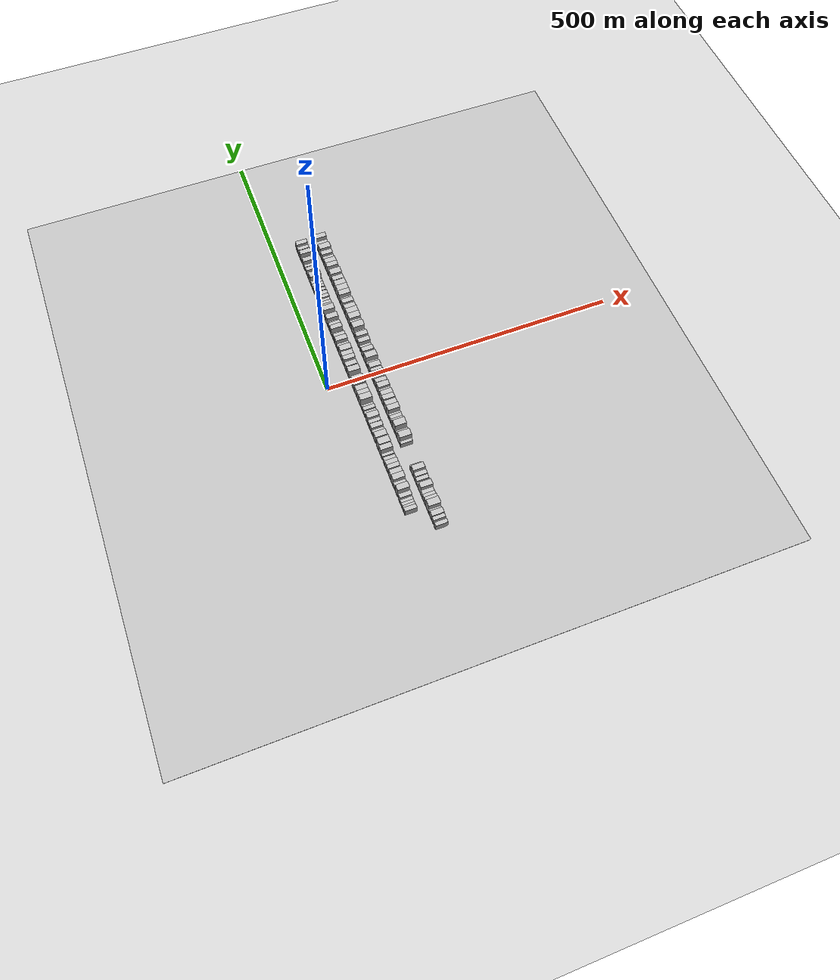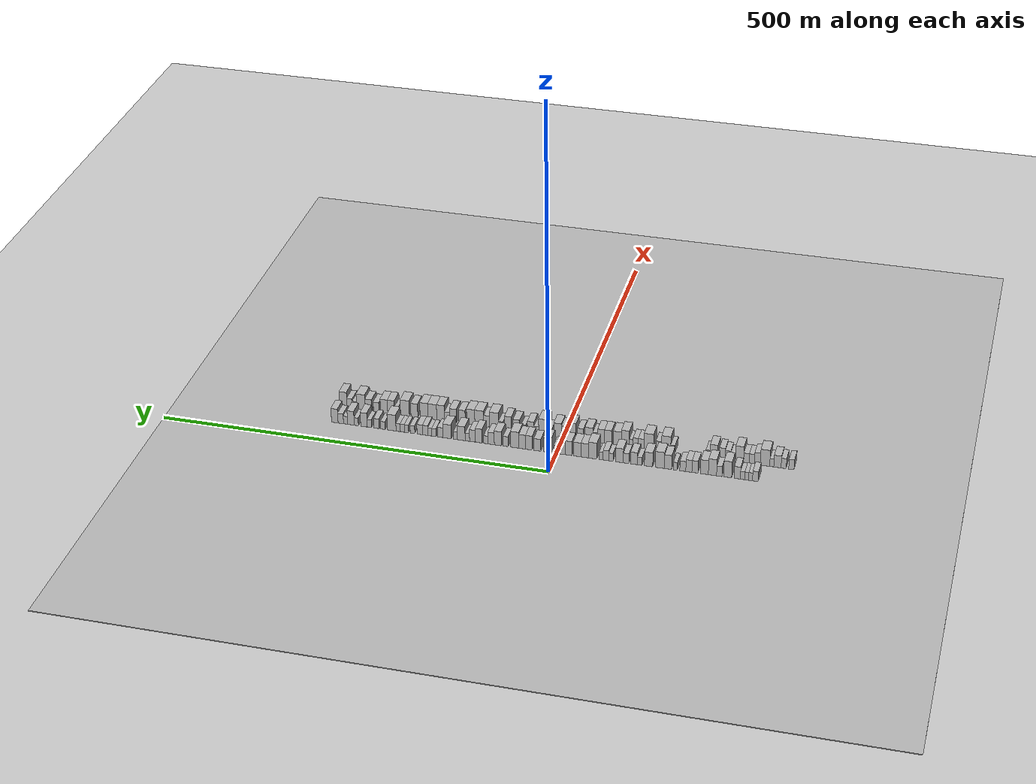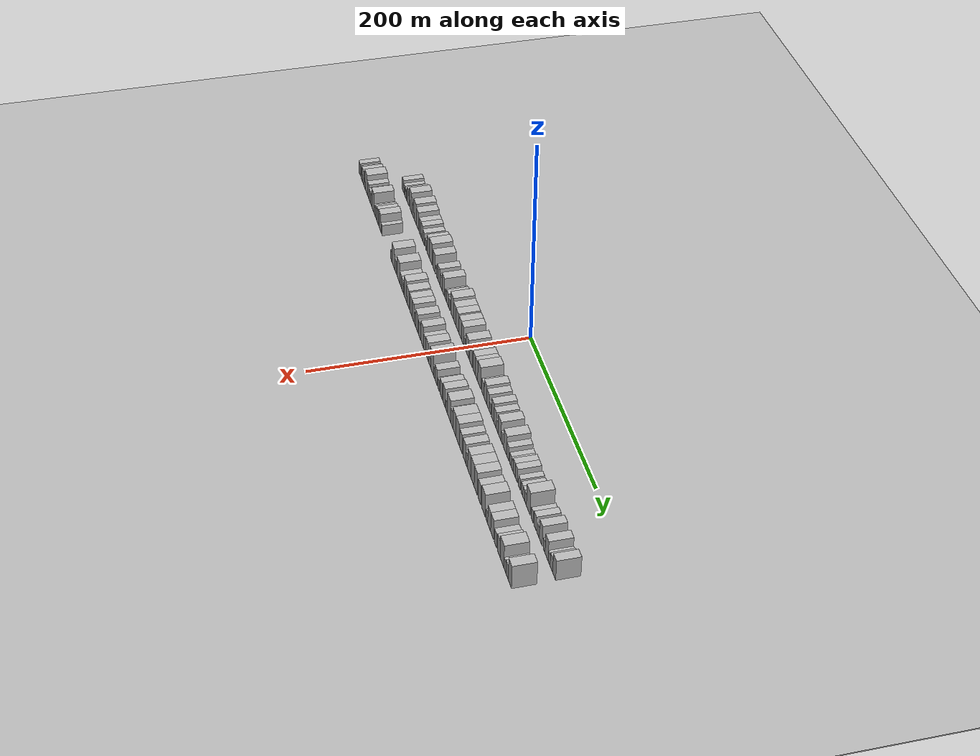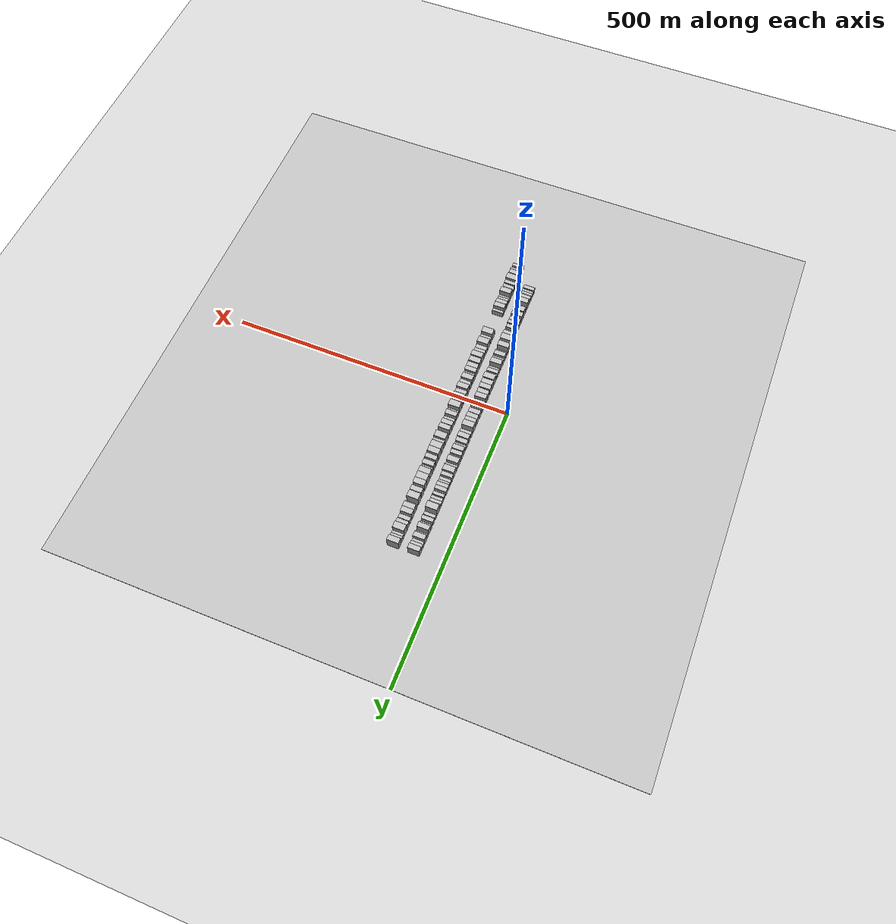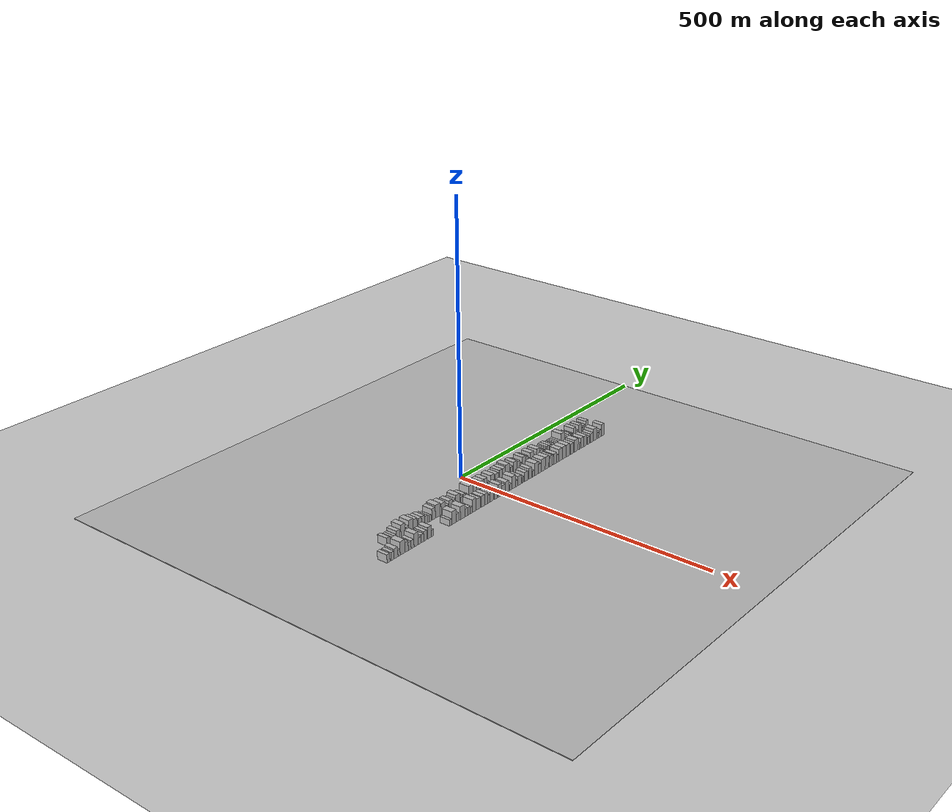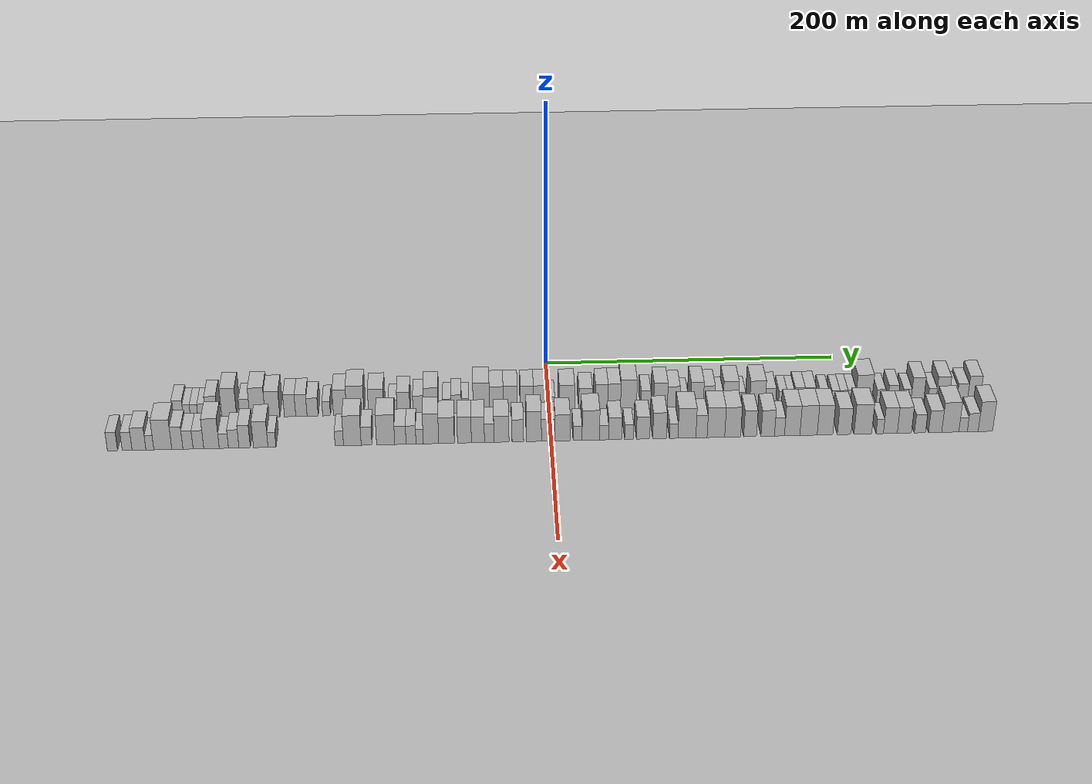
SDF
<?xml version="1.0" encoding="utf-8"?>

<sdf version="1.6">

   <world name="default">

      <gui fullscreen="0">

         <camera name="user_camera">

            <pose>-15 0 4.57585 0 0 0</pose>

            <view_controller>orbit</view_controller>

         </camera>

      </gui>

      <scene>

         <sky>

           <clouds>

             <speed>12</speed>

           </clouds>

         </sky>

         <ambient>0.4 0.4 0.4 1</ambient>

         <background>0.7 0.7 0.7 1</background>

         <shadows>1</shadows>

      </scene>

      <gravity>0 0 -9.8066</gravity>

      <magnetic_field>6e-06 2.3e-05 -4.2e-05</magnetic_field>

      <physics default="0" name="default_physics" type="ode">

         <ode>

            <solver>

               <type>quick</type>

               <iters>10</iters>

               <sor>1.0</sor>

               <use_dynamic_moi_rescaling>0</use_dynamic_moi_rescaling>

            </solver>

            <constraints>

               <cfm>0</cfm>

               <erp>0.2</erp>

               <contact_max_correcting_vel>100</contact_max_correcting_vel>

               <contact_surface_layer>0.001</contact_surface_layer>

            </constraints>

         </ode>

         <max_step_size>0.004</max_step_size>

         <real_time_factor>1</real_time_factor>

         <real_time_update_rate>250</real_time_update_rate>

      </physics>

      <light name="sun" type="directional">

         <cast_shadows>1</cast_shadows>

         <pose>0 0 10 0 0 0</pose>

         <diffuse>0.8 0.8 0.8 1</diffuse>

         <specular>0.2 0.2 0.2 1</specular>

         <attenuation>

            <range>1000</range>

            <constant>0.9</constant>

            <linear>0.01</linear>

            <quadratic>0.001</quadratic>

         </attenuation>

         <direction>-0.5 0.1 -0.9</direction>

      </light>

      <include>

         <name>ground_plane_1</name>

         <uri>model://HANNAS_ground_plane</uri>

         <pose>0 0 0  0 0 0</pose>

      </include>

      <include>

         <name>ground_plane_2</name>

         <uri>model://HANNAS_ground_plane</uri>

         <pose>100 0 0  0 0 0</pose>

      </include>

      <model name="building_1">

         <static>1</static>

         <pose frame="">50.0000 -248.3277 0 0.000000 0.000000 0.000000</pose>

         <link name="link">

            <pose frame="">0 0 7.50 0 0 0</pose>

            <collision name="collision">

               <geometry>

                  <box>

                     <size>20.0000 7.1149 15.0000</size>

                  </box>

               </geometry>

               <max_contacts>10</max_contacts>

               <surface>

                  <contact>

                     <ode/>

                  </contact>

                  <bounce/>

                  <friction>

                     <torsional>

                        <ode/>

                     </torsional>

                     <ode/>

                  </friction>

               </surface>

            </collision>

            <visual name="visual">

               <cast_shadows>0</cast_shadows>

               <geometry>

                  <box>

                     <size>20.0000 7.1149 15.0000</size>

                  </box>

               </geometry>

               <material>

                  <script>

                     <uri>model://HANNAS_wall/materials/scripts</uri>

                     <uri>model://HANNAS_wall/materials/textures</uri>

                     <name>vrc/HANNAS_wall</name>

                  </script>

               </material>

            </visual>

            <self_collide>0</self_collide>

            <enable_wind>0</enable_wind>

            <kinematic>0</kinematic>

         </link>

      </model>

      <model name="building_2">

         <static>1</static>

         <pose frame="">50.0000 -242.3634 0 0.000000 0.000000 0.000000</pose>

         <link name="link">

            <pose frame="">0 0 6.00 0 0 0</pose>

            <collision name="collision">

               <geometry>

                  <box>

                     <size>20.0000 4.8136 12.0000</size>

                  </box>

               </geometry>

               <max_contacts>10</max_contacts>

               <surface>

                  <contact>

                     <ode/>

                  </contact>

                  <bounce/>

                  <friction>

                     <torsional>

                        <ode/>

                     </torsional>

                     <ode/>

                  </friction>

               </surface>

            </collision>

            <visual name="visual">

               <cast_shadows>0</cast_shadows>

               <geometry>

                  <box>

                     <size>20.0000 4.8136 12.0000</size>

                  </box>

               </geometry>

               <material>

                  <script>

                     <uri>model://HANNAS_wall/materials/scripts</uri>

                     <uri>model://HANNAS_wall/materials/textures</uri>

                     <name>vrc/HANNAS_wall</name>

                  </script>

               </material>

            </visual>

            <self_collide>0</self_collide>

            <enable_wind>0</enable_wind>

            <kinematic>0</kinematic>

         </link>

      </model>

      <model name="building_3">

         <static>1</static>

         <pose frame="">50.0000 -237.5000 0 0.000000 0.000000 0.000000</pose>

         <link name="link">

            <pose frame="">0 0 6.00 0 0 0</pose>

            <collision name="collision">

               <geometry>

                  <box>

                     <size>20.0000 4.9132 12.0000</size>

                  </box>

               </geometry>

               <max_contacts>10</max_contacts>

               <surface>

                  <contact>

                     <ode/>

                  </contact>

                  <bounce/>

                  <friction>

                     <torsional>

                        <ode/>

                     </torsional>

                     <ode/>

                  </friction>

               </surface>

            </collision>

            <visual name="visual">

               <cast_shadows>0</cast_shadows>

               <geometry>

                  <box>

                     <size>20.0000 4.9132 12.0000</size>

                  </box>

               </geometry>

               <material>

                  <script>

                     <uri>model://HANNAS_wall/materials/scripts</uri>

                     <uri>model://HANNAS_wall/materials/textures</uri>

                     <name>vrc/HANNAS_wall</name>

                  </script>

               </material>

            </visual>

            <self_collide>0</self_collide>

            <enable_wind>0</enable_wind>

            <kinematic>0</kinematic>

         </link>

      </model>

      <model name="building_4">

         <static>1</static>

         <pose frame="">50.0000 -232.4500 0 0.000000 0.000000 0.000000</pose>

         <link name="link">

            <pose frame="">0 0 6.00 0 0 0</pose>

            <collision name="collision">

               <geometry>

                  <box>

                     <size>20.0000 5.1869 12.0000</size>

                  </box>

               </geometry>

               <max_contacts>10</max_contacts>

               <surface>

                  <contact>

                     <ode/>

                  </contact>

                  <bounce/>

                  <friction>

                     <torsional>

                        <ode/>

                     </torsional>

                     <ode/>

                  </friction>

               </surface>

            </collision>

            <visual name="visual">

               <cast_shadows>0</cast_shadows>

               <geometry>

                  <box>

                     <size>20.0000 5.1869 12.0000</size>

                  </box>

               </geometry>

               <material>

                  <script>

                     <uri>model://HANNAS_wall/materials/scripts</uri>

                     <uri>model://HANNAS_wall/materials/textures</uri>

                     <name>vrc/HANNAS_wall</name>

                  </script>

               </material>

            </visual>

            <self_collide>0</self_collide>

            <enable_wind>0</enable_wind>

            <kinematic>0</kinematic>

         </link>

      </model>

      <model name="building_5">

         <static>1</static>

         <pose frame="">50.0000 -226.0046 0 0.000000 0.000000 0.000000</pose>

         <link name="link">

            <pose frame="">0 0 9.00 0 0 0</pose>

            <collision name="collision">

               <geometry>

                  <box>

                     <size>20.0000 7.7039 18.0000</size>

                  </box>

               </geometry>

               <max_contacts>10</max_contacts>

               <surface>

                  <contact>

                     <ode/>

                  </contact>

                  <bounce/>

                  <friction>

                     <torsional>

                        <ode/>

                     </torsional>

                     <ode/>

                  </friction>

               </surface>

            </collision>

            <visual name="visual">

               <cast_shadows>0</cast_shadows>

               <geometry>

                  <box>

                     <size>20.0000 7.7039 18.0000</size>

                  </box>

               </geometry>

               <material>

                  <script>

                     <uri>model://HANNAS_wall/materials/scripts</uri>

                     <uri>model://HANNAS_wall/materials/textures</uri>

                     <name>vrc/HANNAS_wall</name>

                  </script>

               </material>

            </visual>

            <self_collide>0</self_collide>

            <enable_wind>0</enable_wind>

            <kinematic>0</kinematic>

         </link>

      </model>

      <model name="building_6">

         <static>1</static>

         <pose frame="">50.0000 -214.1947 0 0.000000 0.000000 0.000000</pose>

         <link name="link">

            <pose frame="">0 0 12.00 0 0 0</pose>

            <collision name="collision">

               <geometry>

                  <box>

                     <size>20.0000 9.9158 24.0000</size>

                  </box>

               </geometry>

               <max_contacts>10</max_contacts>

               <surface>

                  <contact>

                     <ode/>

                  </contact>

                  <bounce/>

                  <friction>

                     <torsional>

                        <ode/>

                     </torsional>

                     <ode/>

                  </friction>

               </surface>

            </collision>

            <visual name="visual">

               <cast_shadows>0</cast_shadows>

               <geometry>

                  <box>

                     <size>20.0000 9.9158 24.0000</size>

                  </box>

               </geometry>

               <material>

                  <script>

                     <uri>model://HANNAS_wall/materials/scripts</uri>

                     <uri>model://HANNAS_wall/materials/textures</uri>

                     <name>vrc/HANNAS_wall</name>

                  </script>

               </material>

            </visual>

            <self_collide>0</self_collide>

            <enable_wind>0</enable_wind>

            <kinematic>0</kinematic>

         </link>

      </model>

      <model name="building_7">

         <static>1</static>

         <pose frame="">50.0000 -203.8955 0 0.000000 0.000000 0.000000</pose>

         <link name="link">

            <pose frame="">0 0 7.50 0 0 0</pose>

            <collision name="collision">

               <geometry>

                  <box>

                     <size>20.0000 6.6826 15.0000</size>

                  </box>

               </geometry>

               <max_contacts>10</max_contacts>

               <surface>

                  <contact>

                     <ode/>

                  </contact>

                  <bounce/>

                  <friction>

                     <torsional>

                        <ode/>

                     </torsional>

                     <ode/>

                  </friction>

               </surface>

            </collision>

            <visual name="visual">

               <cast_shadows>0</cast_shadows>

               <geometry>

                  <box>

                     <size>20.0000 6.6826 15.0000</size>

                  </box>

               </geometry>

               <material>

                  <script>

                     <uri>model://HANNAS_wall/materials/scripts</uri>

                     <uri>model://HANNAS_wall/materials/textures</uri>

                     <name>vrc/HANNAS_wall</name>

                  </script>

               </material>

            </visual>

            <self_collide>0</self_collide>

            <enable_wind>0</enable_wind>

            <kinematic>0</kinematic>

         </link>

      </model>

      <model name="building_8">

         <static>1</static>

         <pose frame="">50.0000 -195.4504 0 0.000000 0.000000 0.000000</pose>

         <link name="link">

            <pose frame="">0 0 12.00 0 0 0</pose>

            <collision name="collision">

               <geometry>

                  <box>

                     <size>20.0000 10.2077 24.0000</size>

                  </box>

               </geometry>

               <max_contacts>10</max_contacts>

               <surface>

                  <contact>

                     <ode/>

                  </contact>

                  <bounce/>

                  <friction>

                     <torsional>

                        <ode/>

                     </torsional>

                     <ode/>

                  </friction>

               </surface>

            </collision>

            <visual name="visual">

               <cast_shadows>0</cast_shadows>

               <geometry>

                  <box>

                     <size>20.0000 10.2077 24.0000</size>

                  </box>

               </geometry>

               <material>

                  <script>

                     <uri>model://HANNAS_wall/materials/scripts</uri>

                     <uri>model://HANNAS_wall/materials/textures</uri>

                     <name>vrc/HANNAS_wall</name>

                  </script>

               </material>

            </visual>

            <self_collide>0</self_collide>

            <enable_wind>0</enable_wind>

            <kinematic>0</kinematic>

         </link>

      </model>

      <model name="building_9">

         <static>1</static>

         <pose frame="">50.0000 -185.4617 0 0.000000 0.000000 0.000000</pose>

         <link name="link">

            <pose frame="">0 0 10.50 0 0 0</pose>

            <collision name="collision">

               <geometry>

                  <box>

                     <size>20.0000 9.7698 21.0000</size>

                  </box>

               </geometry>

               <max_contacts>10</max_contacts>

               <surface>

                  <contact>

                     <ode/>

                  </contact>

                  <bounce/>

                  <friction>

                     <torsional>

                        <ode/>

                     </torsional>

                     <ode/>

                  </friction>

               </surface>

            </collision>

            <visual name="visual">

               <cast_shadows>0</cast_shadows>

               <geometry>

                  <box>

                     <size>20.0000 9.7698 21.0000</size>

                  </box>

               </geometry>

               <material>

                  <script>

                     <uri>model://HANNAS_wall/materials/scripts</uri>

                     <uri>model://HANNAS_wall/materials/textures</uri>

                     <name>vrc/HANNAS_wall</name>

                  </script>

               </material>

            </visual>

            <self_collide>0</self_collide>

            <enable_wind>0</enable_wind>

            <kinematic>0</kinematic>

         </link>

      </model>

      <model name="building_10">

         <static>1</static>

         <pose frame="">50.0000 -173.8028 0 0.000000 0.000000 0.000000</pose>

         <link name="link">

            <pose frame="">0 0 9.00 0 0 0</pose>

            <collision name="collision">

               <geometry>

                  <box>

                     <size>20.0000 7.5480 18.0000</size>

                  </box>

               </geometry>

               <max_contacts>10</max_contacts>

               <surface>

                  <contact>

                     <ode/>

                  </contact>

                  <bounce/>

                  <friction>

                     <torsional>

                        <ode/>

                     </torsional>

                     <ode/>

                  </friction>

               </surface>

            </collision>

            <visual name="visual">

               <cast_shadows>0</cast_shadows>

               <geometry>

                  <box>

                     <size>20.0000 7.5480 18.0000</size>

                  </box>

               </geometry>

               <material>

                  <script>

                     <uri>model://HANNAS_wall/materials/scripts</uri>

                     <uri>model://HANNAS_wall/materials/textures</uri>

                     <name>vrc/HANNAS_wall</name>

                  </script>

               </material>

            </visual>

            <self_collide>0</self_collide>

            <enable_wind>0</enable_wind>

            <kinematic>0</kinematic>

         </link>

      </model>

      <model name="building_11">

         <static>1</static>

         <pose frame="">50.0000 -166.2367 0 0.000000 0.000000 0.000000</pose>

         <link name="link">

            <pose frame="">0 0 9.00 0 0 0</pose>

            <collision name="collision">

               <geometry>

                  <box>

                     <size>20.0000 7.5842 18.0000</size>

                  </box>

               </geometry>

               <max_contacts>10</max_contacts>

               <surface>

                  <contact>

                     <ode/>

                  </contact>

                  <bounce/>

                  <friction>

                     <torsional>

                        <ode/>

                     </torsional>

                     <ode/>

                  </friction>

               </surface>

            </collision>

            <visual name="visual">

               <cast_shadows>0</cast_shadows>

               <geometry>

                  <box>

                     <size>20.0000 7.5842 18.0000</size>

                  </box>

               </geometry>

               <material>

                  <script>

                     <uri>model://HANNAS_wall/materials/scripts</uri>

                     <uri>model://HANNAS_wall/materials/textures</uri>

                     <name>vrc/HANNAS_wall</name>

                  </script>

               </material>

            </visual>

            <self_collide>0</self_collide>

            <enable_wind>0</enable_wind>

            <kinematic>0</kinematic>

         </link>

      </model>

      <model name="building_12">

         <static>1</static>

         <pose frame="">50.0000 -158.7453 0 0.000000 0.000000 0.000000</pose>

         <link name="link">

            <pose frame="">0 0 7.50 0 0 0</pose>

            <collision name="collision">

               <geometry>

                  <box>

                     <size>20.0000 7.3986 15.0000</size>

                  </box>

               </geometry>

               <max_contacts>10</max_contacts>

               <surface>

                  <contact>

                     <ode/>

                  </contact>

                  <bounce/>

                  <friction>

                     <torsional>

                        <ode/>

                     </torsional>

                     <ode/>

                  </friction>

               </surface>

            </collision>

            <visual name="visual">

               <cast_shadows>0</cast_shadows>

               <geometry>

                  <box>

                     <size>20.0000 7.3986 15.0000</size>

                  </box>

               </geometry>

               <material>

                  <script>

                     <uri>model://HANNAS_wall/materials/scripts</uri>

                     <uri>model://HANNAS_wall/materials/textures</uri>

                     <name>vrc/HANNAS_wall</name>

                  </script>

               </material>

            </visual>

            <self_collide>0</self_collide>

            <enable_wind>0</enable_wind>

            <kinematic>0</kinematic>

         </link>

      </model>

      <model name="building_13">

         <static>1</static>

         <pose frame="">50.0000 -149.4394 0 0.000000 0.000000 0.000000</pose>

         <link name="link">

            <pose frame="">0 0 6.00 0 0 0</pose>

            <collision name="collision">

               <geometry>

                  <box>

                     <size>20.0000 5.2131 12.0000</size>

                  </box>

               </geometry>

               <max_contacts>10</max_contacts>

               <surface>

                  <contact>

                     <ode/>

                  </contact>

                  <bounce/>

                  <friction>

                     <torsional>

                        <ode/>

                     </torsional>

                     <ode/>

                  </friction>

               </surface>

            </collision>

            <visual name="visual">

               <cast_shadows>0</cast_shadows>

               <geometry>

                  <box>

                     <size>20.0000 5.2131 12.0000</size>

                  </box>

               </geometry>

               <material>

                  <script>

                     <uri>model://HANNAS_wall/materials/scripts</uri>

                     <uri>model://HANNAS_wall/materials/textures</uri>

                     <name>vrc/HANNAS_wall</name>

                  </script>

               </material>

            </visual>

            <self_collide>0</self_collide>

            <enable_wind>0</enable_wind>

            <kinematic>0</kinematic>

         </link>

      </model>

      <model name="building_14">

         <static>1</static>

         <pose frame="">50.0000 -140.3880 0 0.000000 0.000000 0.000000</pose>

         <link name="link">

            <pose frame="">0 0 10.50 0 0 0</pose>

            <collision name="collision">

               <geometry>

                  <box>

                     <size>20.0000 8.8898 21.0000</size>

                  </box>

               </geometry>

               <max_contacts>10</max_contacts>

               <surface>

                  <contact>

                     <ode/>

                  </contact>

                  <bounce/>

                  <friction>

                     <torsional>

                        <ode/>

                     </torsional>

                     <ode/>

                  </friction>

               </surface>

            </collision>

            <visual name="visual">

               <cast_shadows>0</cast_shadows>

               <geometry>

                  <box>

                     <size>20.0000 8.8898 21.0000</size>

                  </box>

               </geometry>

               <material>

                  <script>

                     <uri>model://HANNAS_wall/materials/scripts</uri>

                     <uri>model://HANNAS_wall/materials/textures</uri>

                     <name>vrc/HANNAS_wall</name>

                  </script>

               </material>

            </visual>

            <self_collide>0</self_collide>

            <enable_wind>0</enable_wind>

            <kinematic>0</kinematic>

         </link>

      </model>

      <model name="building_15">

         <static>1</static>

         <pose frame="">50.0000 -130.1336 0 0.000000 0.000000 0.000000</pose>

         <link name="link">

            <pose frame="">0 0 12.00 0 0 0</pose>

            <collision name="collision">

               <geometry>

                  <box>

                     <size>20.0000 11.6189 24.0000</size>

                  </box>

               </geometry>

               <max_contacts>10</max_contacts>

               <surface>

                  <contact>

                     <ode/>

                  </contact>

                  <bounce/>

                  <friction>

                     <torsional>

                        <ode/>

                     </torsional>

                     <ode/>

                  </friction>

               </surface>

            </collision>

            <visual name="visual">

               <cast_shadows>0</cast_shadows>

               <geometry>

                  <box>

                     <size>20.0000 11.6189 24.0000</size>

                  </box>

               </geometry>

               <material>

                  <script>

                     <uri>model://HANNAS_wall/materials/scripts</uri>

                     <uri>model://HANNAS_wall/materials/textures</uri>

                     <name>vrc/HANNAS_wall</name>

                  </script>

               </material>

            </visual>

            <self_collide>0</self_collide>

            <enable_wind>0</enable_wind>

            <kinematic>0</kinematic>

         </link>

      </model>

      <model name="building_16">

         <static>1</static>

         <pose frame="">50.0000 -116.1493 0 0.000000 0.000000 0.000000</pose>

         <link name="link">

            <pose frame="">0 0 10.50 0 0 0</pose>

            <collision name="collision">

               <geometry>

                  <box>

                     <size>20.0000 10.3499 21.0000</size>

                  </box>

               </geometry>

               <max_contacts>10</max_contacts>

               <surface>

                  <contact>

                     <ode/>

                  </contact>

                  <bounce/>

                  <friction>

                     <torsional>

                        <ode/>

                     </torsional>

                     <ode/>

                  </friction>

               </surface>

            </collision>

            <visual name="visual">

               <cast_shadows>0</cast_shadows>

               <geometry>

                  <box>

                     <size>20.0000 10.3499 21.0000</size>

                  </box>

               </geometry>

               <material>

                  <script>

                     <uri>model://HANNAS_wall/materials/scripts</uri>

                     <uri>model://HANNAS_wall/materials/textures</uri>

                     <name>vrc/HANNAS_wall</name>

                  </script>

               </material>

            </visual>

            <self_collide>0</self_collide>

            <enable_wind>0</enable_wind>

            <kinematic>0</kinematic>

         </link>

      </model>

      <model name="building_17">

         <static>1</static>

         <pose frame="">50.0000 -105.0805 0 0.000000 0.000000 0.000000</pose>

         <link name="link">

            <pose frame="">0 0 6.00 0 0 0</pose>

            <collision name="collision">

               <geometry>

                  <box>

                     <size>20.0000 5.7877 12.0000</size>

                  </box>

               </geometry>

               <max_contacts>10</max_contacts>

               <surface>

                  <contact>

                     <ode/>

                  </contact>

                  <bounce/>

                  <friction>

                     <torsional>

                        <ode/>

                     </torsional>

                     <ode/>

                  </friction>

               </surface>

            </collision>

            <visual name="visual">

               <cast_shadows>0</cast_shadows>

               <geometry>

                  <box>

                     <size>20.0000 5.7877 12.0000</size>

                  </box>

               </geometry>

               <material>

                  <script>

                     <uri>model://HANNAS_wall/materials/scripts</uri>

                     <uri>model://HANNAS_wall/materials/textures</uri>

                     <name>vrc/HANNAS_wall</name>

                  </script>

               </material>

            </visual>

            <self_collide>0</self_collide>

            <enable_wind>0</enable_wind>

            <kinematic>0</kinematic>

         </link>

      </model>

      <model name="building_18">

         <static>1</static>

         <pose frame="">50.0000 -97.8839 0 0.000000 0.000000 0.000000</pose>

         <link name="link">

            <pose frame="">0 0 9.00 0 0 0</pose>

            <collision name="collision">

               <geometry>

                  <box>

                     <size>20.0000 8.6054 18.0000</size>

                  </box>

               </geometry>

               <max_contacts>10</max_contacts>

               <surface>

                  <contact>

                     <ode/>

                  </contact>

                  <bounce/>

                  <friction>

                     <torsional>

                        <ode/>

                     </torsional>

                     <ode/>

                  </friction>

               </surface>

            </collision>

            <visual name="visual">

               <cast_shadows>0</cast_shadows>

               <geometry>

                  <box>

                     <size>20.0000 8.6054 18.0000</size>

                  </box>

               </geometry>

               <material>

                  <script>

                     <uri>model://HANNAS_wall/materials/scripts</uri>

                     <uri>model://HANNAS_wall/materials/textures</uri>

                     <name>vrc/HANNAS_wall</name>

                  </script>

               </material>

            </visual>

            <self_collide>0</self_collide>

            <enable_wind>0</enable_wind>

            <kinematic>0</kinematic>

         </link>

      </model>

      <model name="building_19">

         <static>1</static>

         <pose frame="">50.0000 -88.0649 0 0.000000 0.000000 0.000000</pose>

         <link name="link">

            <pose frame="">0 0 7.50 0 0 0</pose>

            <collision name="collision">

               <geometry>

                  <box>

                     <size>20.0000 7.0328 15.0000</size>

                  </box>

               </geometry>

               <max_contacts>10</max_contacts>

               <surface>

                  <contact>

                     <ode/>

                  </contact>

                  <bounce/>

                  <friction>

                     <torsional>

                        <ode/>

                     </torsional>

                     <ode/>

                  </friction>

               </surface>

            </collision>

            <visual name="visual">

               <cast_shadows>0</cast_shadows>

               <geometry>

                  <box>

                     <size>20.0000 7.0328 15.0000</size>

                  </box>

               </geometry>

               <material>

                  <script>

                     <uri>model://HANNAS_wall/materials/scripts</uri>

                     <uri>model://HANNAS_wall/materials/textures</uri>

                     <name>vrc/HANNAS_wall</name>

                  </script>

               </material>

            </visual>

            <self_collide>0</self_collide>

            <enable_wind>0</enable_wind>

            <kinematic>0</kinematic>

         </link>

      </model>

      <model name="building_20">

         <static>1</static>

         <pose frame="">50.0000 -79.5889 0 0.000000 0.000000 0.000000</pose>

         <link name="link">

            <pose frame="">0 0 10.50 0 0 0</pose>

            <collision name="collision">

               <geometry>

                  <box>

                     <size>20.0000 9.9191 21.0000</size>

                  </box>

               </geometry>

               <max_contacts>10</max_contacts>

               <surface>

                  <contact>

                     <ode/>

                  </contact>

                  <bounce/>

                  <friction>

                     <torsional>

                        <ode/>

                     </torsional>

                     <ode/>

                  </friction>

               </surface>

            </collision>

            <visual name="visual">

               <cast_shadows>0</cast_shadows>

               <geometry>

                  <box>

                     <size>20.0000 9.9191 21.0000</size>

                  </box>

               </geometry>

               <material>

                  <script>

                     <uri>model://HANNAS_wall/materials/scripts</uri>

                     <uri>model://HANNAS_wall/materials/textures</uri>

                     <name>vrc/HANNAS_wall</name>

                  </script>

               </material>

            </visual>

            <self_collide>0</self_collide>

            <enable_wind>0</enable_wind>

            <kinematic>0</kinematic>

         </link>

      </model>

      <model name="building_21">

         <static>1</static>

         <pose frame="">50.0000 -68.9209 0 0.000000 0.000000 0.000000</pose>

         <link name="link">

            <pose frame="">0 0 6.00 0 0 0</pose>

            <collision name="collision">

               <geometry>

                  <box>

                     <size>20.0000 5.4170 12.0000</size>

                  </box>

               </geometry>

               <max_contacts>10</max_contacts>

               <surface>

                  <contact>

                     <ode/>

                  </contact>

                  <bounce/>

                  <friction>

                     <torsional>

                        <ode/>

                     </torsional>

                     <ode/>

                  </friction>

               </surface>

            </collision>

            <visual name="visual">

               <cast_shadows>0</cast_shadows>

               <geometry>

                  <box>

                     <size>20.0000 5.4170 12.0000</size>

                  </box>

               </geometry>

               <material>

                  <script>

                     <uri>model://HANNAS_wall/materials/scripts</uri>

                     <uri>model://HANNAS_wall/materials/textures</uri>

                     <name>vrc/HANNAS_wall</name>

                  </script>

               </material>

            </visual>

            <self_collide>0</self_collide>

            <enable_wind>0</enable_wind>

            <kinematic>0</kinematic>

         </link>

      </model>

      <model name="building_22">

         <static>1</static>

         <pose frame="">50.0000 -62.6847 0 0.000000 0.000000 0.000000</pose>

         <link name="link">

            <pose frame="">0 0 7.50 0 0 0</pose>

            <collision name="collision">

               <geometry>

                  <box>

                     <size>20.0000 7.0552 15.0000</size>

                  </box>

               </geometry>

               <max_contacts>10</max_contacts>

               <surface>

                  <contact>

                     <ode/>

                  </contact>

                  <bounce/>

                  <friction>

                     <torsional>

                        <ode/>

                     </torsional>

                     <ode/>

                  </friction>

               </surface>

            </collision>

            <visual name="visual">

               <cast_shadows>0</cast_shadows>

               <geometry>

                  <box>

                     <size>20.0000 7.0552 15.0000</size>

                  </box>

               </geometry>

               <material>

                  <script>

                     <uri>model://HANNAS_wall/materials/scripts</uri>

                     <uri>model://HANNAS_wall/materials/textures</uri>

                     <name>vrc/HANNAS_wall</name>

                  </script>

               </material>

            </visual>

            <self_collide>0</self_collide>

            <enable_wind>0</enable_wind>

            <kinematic>0</kinematic>

         </link>

      </model>

      <model name="building_23">

         <static>1</static>

         <pose frame="">50.0000 -56.7431 0 0.000000 0.000000 0.000000</pose>

         <link name="link">

            <pose frame="">0 0 6.00 0 0 0</pose>

            <collision name="collision">

               <geometry>

                  <box>

                     <size>20.0000 4.8282 12.0000</size>

                  </box>

               </geometry>

               <max_contacts>10</max_contacts>

               <surface>

                  <contact>

                     <ode/>

                  </contact>

                  <bounce/>

                  <friction>

                     <torsional>

                        <ode/>

                     </torsional>

                     <ode/>

                  </friction>

               </surface>

            </collision>

            <visual name="visual">

               <cast_shadows>0</cast_shadows>

               <geometry>

                  <box>

                     <size>20.0000 4.8282 12.0000</size>

                  </box>

               </geometry>

               <material>

                  <script>

                     <uri>model://HANNAS_wall/materials/scripts</uri>

                     <uri>model://HANNAS_wall/materials/textures</uri>

                     <name>vrc/HANNAS_wall</name>

                  </script>

               </material>

            </visual>

            <self_collide>0</self_collide>

            <enable_wind>0</enable_wind>

            <kinematic>0</kinematic>

         </link>

      </model>

      <model name="building_24">

         <static>1</static>

         <pose frame="">50.0000 -45.8779 0 0.000000 0.000000 0.000000</pose>

         <link name="link">

            <pose frame="">0 0 12.00 0 0 0</pose>

            <collision name="collision">

               <geometry>

                  <box>

                     <size>20.0000 10.9021 24.0000</size>

                  </box>

               </geometry>

               <max_contacts>10</max_contacts>

               <surface>

                  <contact>

                     <ode/>

                  </contact>

                  <bounce/>

                  <friction>

                     <torsional>

                        <ode/>

                     </torsional>

                     <ode/>

                  </friction>

               </surface>

            </collision>

            <visual name="visual">

               <cast_shadows>0</cast_shadows>

               <geometry>

                  <box>

                     <size>20.0000 10.9021 24.0000</size>

                  </box>

               </geometry>

               <material>

                  <script>

                     <uri>model://HANNAS_wall/materials/scripts</uri>

                     <uri>model://HANNAS_wall/materials/textures</uri>

                     <name>vrc/HANNAS_wall</name>

                  </script>

               </material>

            </visual>

            <self_collide>0</self_collide>

            <enable_wind>0</enable_wind>

            <kinematic>0</kinematic>

         </link>

      </model>

      <model name="building_25">

         <static>1</static>

         <pose frame="">50.0000 -35.7782 0 0.000000 0.000000 0.000000</pose>

         <link name="link">

            <pose frame="">0 0 10.50 0 0 0</pose>

            <collision name="collision">

               <geometry>

                  <box>

                     <size>20.0000 9.2973 21.0000</size>

                  </box>

               </geometry>

               <max_contacts>10</max_contacts>

               <surface>

                  <contact>

                     <ode/>

                  </contact>

                  <bounce/>

                  <friction>

                     <torsional>

                        <ode/>

                     </torsional>

                     <ode/>

                  </friction>

               </surface>

            </collision>

            <visual name="visual">

               <cast_shadows>0</cast_shadows>

               <geometry>

                  <box>

                     <size>20.0000 9.2973 21.0000</size>

                  </box>

               </geometry>

               <material>

                  <script>

                     <uri>model://HANNAS_wall/materials/scripts</uri>

                     <uri>model://HANNAS_wall/materials/textures</uri>

                     <name>vrc/HANNAS_wall</name>

                  </script>

               </material>

            </visual>

            <self_collide>0</self_collide>

            <enable_wind>0</enable_wind>

            <kinematic>0</kinematic>

         </link>

      </model>

      <model name="building_26">

         <static>1</static>

         <pose frame="">50.0000 -26.3639 0 0.000000 0.000000 0.000000</pose>

         <link name="link">

            <pose frame="">0 0 10.50 0 0 0</pose>

            <collision name="collision">

               <geometry>

                  <box>

                     <size>20.0000 9.5312 21.0000</size>

                  </box>

               </geometry>

               <max_contacts>10</max_contacts>

               <surface>

                  <contact>

                     <ode/>

                  </contact>

                  <bounce/>

                  <friction>

                     <torsional>

                        <ode/>

                     </torsional>

                     <ode/>

                  </friction>

               </surface>

            </collision>

            <visual name="visual">

               <cast_shadows>0</cast_shadows>

               <geometry>

                  <box>

                     <size>20.0000 9.5312 21.0000</size>

                  </box>

               </geometry>

               <material>

                  <script>

                     <uri>model://HANNAS_wall/materials/scripts</uri>

                     <uri>model://HANNAS_wall/materials/textures</uri>

                     <name>vrc/HANNAS_wall</name>

                  </script>

               </material>

            </visual>

            <self_collide>0</self_collide>

            <enable_wind>0</enable_wind>

            <kinematic>0</kinematic>

         </link>

      </model>

      <model name="building_27">

         <static>1</static>

         <pose frame="">50.0000 -15.2484 0 0.000000 0.000000 0.000000</pose>

         <link name="link">

            <pose frame="">0 0 10.50 0 0 0</pose>

            <collision name="collision">

               <geometry>

                  <box>

                     <size>20.0000 8.6997 21.0000</size>

                  </box>

               </geometry>

               <max_contacts>10</max_contacts>

               <surface>

                  <contact>

                     <ode/>

                  </contact>

                  <bounce/>

                  <friction>

                     <torsional>

                        <ode/>

                     </torsional>

                     <ode/>

                  </friction>

               </surface>

            </collision>

            <visual name="visual">

               <cast_shadows>0</cast_shadows>

               <geometry>

                  <box>

                     <size>20.0000 8.6997 21.0000</size>

                  </box>

               </geometry>

               <material>

                  <script>

                     <uri>model://HANNAS_wall/materials/scripts</uri>

                     <uri>model://HANNAS_wall/materials/textures</uri>

                     <name>vrc/HANNAS_wall</name>

                  </script>

               </material>

            </visual>

            <self_collide>0</self_collide>

            <enable_wind>0</enable_wind>

            <kinematic>0</kinematic>

         </link>

      </model>

      <model name="building_28">

         <static>1</static>

         <pose frame="">50.0000 -6.4340 0 0.000000 0.000000 0.000000</pose>

         <link name="link">

            <pose frame="">0 0 10.50 0 0 0</pose>

            <collision name="collision">

               <geometry>

                  <box>

                     <size>20.0000 8.9290 21.0000</size>

                  </box>

               </geometry>

               <max_contacts>10</max_contacts>

               <surface>

                  <contact>

                     <ode/>

                  </contact>

                  <bounce/>

                  <friction>

                     <torsional>

                        <ode/>

                     </torsional>

                     <ode/>

                  </friction>

               </surface>

            </collision>

            <visual name="visual">

               <cast_shadows>0</cast_shadows>

               <geometry>

                  <box>

                     <size>20.0000 8.9290 21.0000</size>

                  </box>

               </geometry>

               <material>

                  <script>

                     <uri>model://HANNAS_wall/materials/scripts</uri>

                     <uri>model://HANNAS_wall/materials/textures</uri>

                     <name>vrc/HANNAS_wall</name>

                  </script>

               </material>

            </visual>

            <self_collide>0</self_collide>

            <enable_wind>0</enable_wind>

            <kinematic>0</kinematic>

         </link>

      </model>

      <model name="building_29">

         <static>1</static>

         <pose frame="">50.0000 0.7145 0 0.000000 0.000000 0.000000</pose>

         <link name="link">

            <pose frame="">0 0 6.00 0 0 0</pose>

            <collision name="collision">

               <geometry>

                  <box>

                     <size>20.0000 5.3681 12.0000</size>

                  </box>

               </geometry>

               <max_contacts>10</max_contacts>

               <surface>

                  <contact>

                     <ode/>

                  </contact>

                  <bounce/>

                  <friction>

                     <torsional>

                        <ode/>

                     </torsional>

                     <ode/>

                  </friction>

               </surface>

            </collision>

            <visual name="visual">

               <cast_shadows>0</cast_shadows>

               <geometry>

                  <box>

                     <size>20.0000 5.3681 12.0000</size>

                  </box>

               </geometry>

               <material>

                  <script>

                     <uri>model://HANNAS_wall/materials/scripts</uri>

                     <uri>model://HANNAS_wall/materials/textures</uri>

                     <name>vrc/HANNAS_wall</name>

                  </script>

               </material>

            </visual>

            <self_collide>0</self_collide>

            <enable_wind>0</enable_wind>

            <kinematic>0</kinematic>

         </link>

      </model>

      <model name="building_30">

         <static>1</static>

         <pose frame="">50.0000 11.5483 0 0.000000 0.000000 0.000000</pose>

         <link name="link">

            <pose frame="">0 0 10.50 0 0 0</pose>

            <collision name="collision">

               <geometry>

                  <box>

                     <size>20.0000 10.2995 21.0000</size>

                  </box>

               </geometry>

               <max_contacts>10</max_contacts>

               <surface>

                  <contact>

                     <ode/>

                  </contact>

                  <bounce/>

                  <friction>

                     <torsional>

                        <ode/>

                     </torsional>

                     <ode/>

                  </friction>

               </surface>

            </collision>

            <visual name="visual">

               <cast_shadows>0</cast_shadows>

               <geometry>

                  <box>

                     <size>20.0000 10.2995 21.0000</size>

                  </box>

               </geometry>

               <material>

                  <script>

                     <uri>model://HANNAS_wall/materials/scripts</uri>

                     <uri>model://HANNAS_wall/materials/textures</uri>

                     <name>vrc/HANNAS_wall</name>

                  </script>

               </material>

            </visual>

            <self_collide>0</self_collide>

            <enable_wind>0</enable_wind>

            <kinematic>0</kinematic>

         </link>

      </model>

      <model name="building_31">

         <static>1</static>

         <pose frame="">50.0000 24.1749 0 0.000000 0.000000 0.000000</pose>

         <link name="link">

            <pose frame="">0 0 9.00 0 0 0</pose>

            <collision name="collision">

               <geometry>

                  <box>

                     <size>20.0000 8.9537 18.0000</size>

                  </box>

               </geometry>

               <max_contacts>10</max_contacts>

               <surface>

                  <contact>

                     <ode/>

                  </contact>

                  <bounce/>

                  <friction>

                     <torsional>

                        <ode/>

                     </torsional>

                     <ode/>

                  </friction>

               </surface>

            </collision>

            <visual name="visual">

               <cast_shadows>0</cast_shadows>

               <geometry>

                  <box>

                     <size>20.0000 8.9537 18.0000</size>

                  </box>

               </geometry>

               <material>

                  <script>

                     <uri>model://HANNAS_wall/materials/scripts</uri>

                     <uri>model://HANNAS_wall/materials/textures</uri>

                     <name>vrc/HANNAS_wall</name>

                  </script>

               </material>

            </visual>

            <self_collide>0</self_collide>

            <enable_wind>0</enable_wind>

            <kinematic>0</kinematic>

         </link>

      </model>

      <model name="building_32">

         <static>1</static>

         <pose frame="">50.0000 34.8956 0 0.000000 0.000000 0.000000</pose>

         <link name="link">

            <pose frame="">0 0 10.50 0 0 0</pose>

            <collision name="collision">

               <geometry>

                  <box>

                     <size>20.0000 8.4877 21.0000</size>

                  </box>

               </geometry>

               <max_contacts>10</max_contacts>

               <surface>

                  <contact>

                     <ode/>

                  </contact>

                  <bounce/>

                  <friction>

                     <torsional>

                        <ode/>

                     </torsional>

                     <ode/>

                  </friction>

               </surface>

            </collision>

            <visual name="visual">

               <cast_shadows>0</cast_shadows>

               <geometry>

                  <box>

                     <size>20.0000 8.4877 21.0000</size>

                  </box>

               </geometry>

               <material>

                  <script>

                     <uri>model://HANNAS_wall/materials/scripts</uri>

                     <uri>model://HANNAS_wall/materials/textures</uri>

                     <name>vrc/HANNAS_wall</name>

                  </script>

               </material>

            </visual>

            <self_collide>0</self_collide>

            <enable_wind>0</enable_wind>

            <kinematic>0</kinematic>

         </link>

      </model>

      <model name="building_33">

         <static>1</static>

         <pose frame="">50.0000 43.4149 0 0.000000 0.000000 0.000000</pose>

         <link name="link">

            <pose frame="">0 0 10.50 0 0 0</pose>

            <collision name="collision">

               <geometry>

                  <box>

                     <size>20.0000 8.5508 21.0000</size>

                  </box>

               </geometry>

               <max_contacts>10</max_contacts>

               <surface>

                  <contact>

                     <ode/>

                  </contact>

                  <bounce/>

                  <friction>

                     <torsional>

                        <ode/>

                     </torsional>

                     <ode/>

                  </friction>

               </surface>

            </collision>

            <visual name="visual">

               <cast_shadows>0</cast_shadows>

               <geometry>

                  <box>

                     <size>20.0000 8.5508 21.0000</size>

                  </box>

               </geometry>

               <material>

                  <script>

                     <uri>model://HANNAS_wall/materials/scripts</uri>

                     <uri>model://HANNAS_wall/materials/textures</uri>

                     <name>vrc/HANNAS_wall</name>

                  </script>

               </material>

            </visual>

            <self_collide>0</self_collide>

            <enable_wind>0</enable_wind>

            <kinematic>0</kinematic>

         </link>

      </model>

      <model name="building_34">

         <static>1</static>

         <pose frame="">50.0000 53.0832 0 0.000000 0.000000 0.000000</pose>

         <link name="link">

            <pose frame="">0 0 12.00 0 0 0</pose>

            <collision name="collision">

               <geometry>

                  <box>

                     <size>20.0000 10.7860 24.0000</size>

                  </box>

               </geometry>

               <max_contacts>10</max_contacts>

               <surface>

                  <contact>

                     <ode/>

                  </contact>

                  <bounce/>

                  <friction>

                     <torsional>

                        <ode/>

                     </torsional>

                     <ode/>

                  </friction>

               </surface>

            </collision>

            <visual name="visual">

               <cast_shadows>0</cast_shadows>

               <geometry>

                  <box>

                     <size>20.0000 10.7860 24.0000</size>

                  </box>

               </geometry>

               <material>

                  <script>

                     <uri>model://HANNAS_wall/materials/scripts</uri>

                     <uri>model://HANNAS_wall/materials/textures</uri>

                     <name>vrc/HANNAS_wall</name>

                  </script>

               </material>

            </visual>

            <self_collide>0</self_collide>

            <enable_wind>0</enable_wind>

            <kinematic>0</kinematic>

         </link>

      </model>

      <model name="building_35">

         <static>1</static>

         <pose frame="">50.0000 64.6992 0 0.000000 0.000000 0.000000</pose>

         <link name="link">

            <pose frame="">0 0 7.50 0 0 0</pose>

            <collision name="collision">

               <geometry>

                  <box>

                     <size>20.0000 6.4458 15.0000</size>

                  </box>

               </geometry>

               <max_contacts>10</max_contacts>

               <surface>

                  <contact>

                     <ode/>

                  </contact>

                  <bounce/>

                  <friction>

                     <torsional>

                        <ode/>

                     </torsional>

                     <ode/>

                  </friction>

               </surface>

            </collision>

            <visual name="visual">

               <cast_shadows>0</cast_shadows>

               <geometry>

                  <box>

                     <size>20.0000 6.4458 15.0000</size>

                  </box>

               </geometry>

               <material>

                  <script>

                     <uri>model://HANNAS_wall/materials/scripts</uri>

                     <uri>model://HANNAS_wall/materials/textures</uri>

                     <name>vrc/HANNAS_wall</name>

                  </script>

               </material>

            </visual>

            <self_collide>0</self_collide>

            <enable_wind>0</enable_wind>

            <kinematic>0</kinematic>

         </link>

      </model>

      <model name="building_36">

         <static>1</static>

         <pose frame="">50.0000 74.5765 0 0.000000 0.000000 0.000000</pose>

         <link name="link">

            <pose frame="">0 0 10.50 0 0 0</pose>

            <collision name="collision">

               <geometry>

                  <box>

                     <size>20.0000 9.3089 21.0000</size>

                  </box>

               </geometry>

               <max_contacts>10</max_contacts>

               <surface>

                  <contact>

                     <ode/>

                  </contact>

                  <bounce/>

                  <friction>

                     <torsional>

                        <ode/>

                     </torsional>

                     <ode/>

                  </friction>

               </surface>

            </collision>

            <visual name="visual">

               <cast_shadows>0</cast_shadows>

               <geometry>

                  <box>

                     <size>20.0000 9.3089 21.0000</size>

                  </box>

               </geometry>

               <material>

                  <script>

                     <uri>model://HANNAS_wall/materials/scripts</uri>

                     <uri>model://HANNAS_wall/materials/textures</uri>

                     <name>vrc/HANNAS_wall</name>

                  </script>

               </material>

            </visual>

            <self_collide>0</self_collide>

            <enable_wind>0</enable_wind>

            <kinematic>0</kinematic>

         </link>

      </model>

      <model name="building_37">

         <static>1</static>

         <pose frame="">50.0000 83.3503 0 0.000000 0.000000 0.000000</pose>

         <link name="link">

            <pose frame="">0 0 9.00 0 0 0</pose>

            <collision name="collision">

               <geometry>

                  <box>

                     <size>20.0000 8.2386 18.0000</size>

                  </box>

               </geometry>

               <max_contacts>10</max_contacts>

               <surface>

                  <contact>

                     <ode/>

                  </contact>

                  <bounce/>

                  <friction>

                     <torsional>

                        <ode/>

                     </torsional>

                     <ode/>

                  </friction>

               </surface>

            </collision>

            <visual name="visual">

               <cast_shadows>0</cast_shadows>

               <geometry>

                  <box>

                     <size>20.0000 8.2386 18.0000</size>

                  </box>

               </geometry>

               <material>

                  <script>

                     <uri>model://HANNAS_wall/materials/scripts</uri>

                     <uri>model://HANNAS_wall/materials/textures</uri>

                     <name>vrc/HANNAS_wall</name>

                  </script>

               </material>

            </visual>

            <self_collide>0</self_collide>

            <enable_wind>0</enable_wind>

            <kinematic>0</kinematic>

         </link>

      </model>

      <model name="building_38">

         <static>1</static>

         <pose frame="">50.0000 90.1507 0 0.000000 0.000000 0.000000</pose>

         <link name="link">

            <pose frame="">0 0 6.00 0 0 0</pose>

            <collision name="collision">

               <geometry>

                  <box>

                     <size>20.0000 5.3623 12.0000</size>

                  </box>

               </geometry>

               <max_contacts>10</max_contacts>

               <surface>

                  <contact>

                     <ode/>

                  </contact>

                  <bounce/>

                  <friction>

                     <torsional>

                        <ode/>

                     </torsional>

                     <ode/>

                  </friction>

               </surface>

            </collision>

            <visual name="visual">

               <cast_shadows>0</cast_shadows>

               <geometry>

                  <box>

                     <size>20.0000 5.3623 12.0000</size>

                  </box>

               </geometry>

               <material>

                  <script>

                     <uri>model://HANNAS_wall/materials/scripts</uri>

                     <uri>model://HANNAS_wall/materials/textures</uri>

                     <name>vrc/HANNAS_wall</name>

                  </script>

               </material>

            </visual>

            <self_collide>0</self_collide>

            <enable_wind>0</enable_wind>

            <kinematic>0</kinematic>

         </link>

      </model>

      <model name="building_39">

         <static>1</static>

         <pose frame="">50.0000 99.1289 0 0.000000 0.000000 0.000000</pose>

         <link name="link">

            <pose frame="">0 0 10.50 0 0 0</pose>

            <collision name="collision">

               <geometry>

                  <box>

                     <size>20.0000 8.5942 21.0000</size>

                  </box>

               </geometry>

               <max_contacts>10</max_contacts>

               <surface>

                  <contact>

                     <ode/>

                  </contact>

                  <bounce/>

                  <friction>

                     <torsional>

                        <ode/>

                     </torsional>

                     <ode/>

                  </friction>

               </surface>

            </collision>

            <visual name="visual">

               <cast_shadows>0</cast_shadows>

               <geometry>

                  <box>

                     <size>20.0000 8.5942 21.0000</size>

                  </box>

               </geometry>

               <material>

                  <script>

                     <uri>model://HANNAS_wall/materials/scripts</uri>

                     <uri>model://HANNAS_wall/materials/textures</uri>

                     <name>vrc/HANNAS_wall</name>

                  </script>

               </material>

            </visual>

            <self_collide>0</self_collide>

            <enable_wind>0</enable_wind>

            <kinematic>0</kinematic>

         </link>

      </model>

      <model name="building_40">

         <static>1</static>

         <pose frame="">50.0000 107.2509 0 0.000000 0.000000 0.000000</pose>

         <link name="link">

            <pose frame="">0 0 9.00 0 0 0</pose>

            <collision name="collision">

               <geometry>

                  <box>

                     <size>20.0000 7.6497 18.0000</size>

                  </box>

               </geometry>

               <max_contacts>10</max_contacts>

               <surface>

                  <contact>

                     <ode/>

                  </contact>

                  <bounce/>

                  <friction>

                     <torsional>

                        <ode/>

                     </torsional>

                     <ode/>

                  </friction>

               </surface>

            </collision>

            <visual name="visual">

               <cast_shadows>0</cast_shadows>

               <geometry>

                  <box>

                     <size>20.0000 7.6497 18.0000</size>

                  </box>

               </geometry>

               <material>

                  <script>

                     <uri>model://HANNAS_wall/materials/scripts</uri>

                     <uri>model://HANNAS_wall/materials/textures</uri>

                     <name>vrc/HANNAS_wall</name>

                  </script>

               </material>

            </visual>

            <self_collide>0</self_collide>

            <enable_wind>0</enable_wind>

            <kinematic>0</kinematic>

         </link>

      </model>

      <model name="building_41">

         <static>1</static>

         <pose frame="">50.0000 113.9115 0 0.000000 0.000000 0.000000</pose>

         <link name="link">

            <pose frame="">0 0 6.00 0 0 0</pose>

            <collision name="collision">

               <geometry>

                  <box>

                     <size>20.0000 5.6714 12.0000</size>

                  </box>

               </geometry>

               <max_contacts>10</max_contacts>

               <surface>

                  <contact>

                     <ode/>

                  </contact>

                  <bounce/>

                  <friction>

                     <torsional>

                        <ode/>

                     </torsional>

                     <ode/>

                  </friction>

               </surface>

            </collision>

            <visual name="visual">

               <cast_shadows>0</cast_shadows>

               <geometry>

                  <box>

                     <size>20.0000 5.6714 12.0000</size>

                  </box>

               </geometry>

               <material>

                  <script>

                     <uri>model://HANNAS_wall/materials/scripts</uri>

                     <uri>model://HANNAS_wall/materials/textures</uri>

                     <name>vrc/HANNAS_wall</name>

                  </script>

               </material>

            </visual>

            <self_collide>0</self_collide>

            <enable_wind>0</enable_wind>

            <kinematic>0</kinematic>

         </link>

      </model>

      <model name="building_42">

         <static>1</static>

         <pose frame="">50.0000 121.8345 0 0.000000 0.000000 0.000000</pose>

         <link name="link">

            <pose frame="">0 0 10.50 0 0 0</pose>

            <collision name="collision">

               <geometry>

                  <box>

                     <size>20.0000 10.1746 21.0000</size>

                  </box>

               </geometry>

               <max_contacts>10</max_contacts>

               <surface>

                  <contact>

                     <ode/>

                  </contact>

                  <bounce/>

                  <friction>

                     <torsional>

                        <ode/>

                     </torsional>

                     <ode/>

                  </friction>

               </surface>

            </collision>

            <visual name="visual">

               <cast_shadows>0</cast_shadows>

               <geometry>

                  <box>

                     <size>20.0000 10.1746 21.0000</size>

                  </box>

               </geometry>

               <material>

                  <script>

                     <uri>model://HANNAS_wall/materials/scripts</uri>

                     <uri>model://HANNAS_wall/materials/textures</uri>

                     <name>vrc/HANNAS_wall</name>

                  </script>

               </material>

            </visual>

            <self_collide>0</self_collide>

            <enable_wind>0</enable_wind>

            <kinematic>0</kinematic>

         </link>

      </model>

      <model name="building_43">

         <static>1</static>

         <pose frame="">50.0000 129.3397 0 0.000000 0.000000 0.000000</pose>

         <link name="link">

            <pose frame="">0 0 6.00 0 0 0</pose>

            <collision name="collision">

               <geometry>

                  <box>

                     <size>20.0000 4.8359 12.0000</size>

                  </box>

               </geometry>

               <max_contacts>10</max_contacts>

               <surface>

                  <contact>

                     <ode/>

                  </contact>

                  <bounce/>

                  <friction>

                     <torsional>

                        <ode/>

                     </torsional>

                     <ode/>

                  </friction>

               </surface>

            </collision>

            <visual name="visual">

               <cast_shadows>0</cast_shadows>

               <geometry>

                  <box>

                     <size>20.0000 4.8359 12.0000</size>

                  </box>

               </geometry>

               <material>

                  <script>

                     <uri>model://HANNAS_wall/materials/scripts</uri>

                     <uri>model://HANNAS_wall/materials/textures</uri>

                     <name>vrc/HANNAS_wall</name>

                  </script>

               </material>

            </visual>

            <self_collide>0</self_collide>

            <enable_wind>0</enable_wind>

            <kinematic>0</kinematic>

         </link>

      </model>

      <model name="building_44">

         <static>1</static>

         <pose frame="">50.0000 139.9928 0 0.000000 0.000000 0.000000</pose>

         <link name="link">

            <pose frame="">0 0 10.50 0 0 0</pose>

            <collision name="collision">

               <geometry>

                  <box>

                     <size>20.0000 10.4704 21.0000</size>

                  </box>

               </geometry>

               <max_contacts>10</max_contacts>

               <surface>

                  <contact>

                     <ode/>

                  </contact>

                  <bounce/>

                  <friction>

                     <torsional>

                        <ode/>

                     </torsional>

                     <ode/>

                  </friction>

               </surface>

            </collision>

            <visual name="visual">

               <cast_shadows>0</cast_shadows>

               <geometry>

                  <box>

                     <size>20.0000 10.4704 21.0000</size>

                  </box>

               </geometry>

               <material>

                  <script>

                     <uri>model://HANNAS_wall/materials/scripts</uri>

                     <uri>model://HANNAS_wall/materials/textures</uri>

                     <name>vrc/HANNAS_wall</name>

                  </script>

               </material>

            </visual>

            <self_collide>0</self_collide>

            <enable_wind>0</enable_wind>

            <kinematic>0</kinematic>

         </link>

      </model>

      <model name="building_45">

         <static>1</static>

         <pose frame="">50.0000 148.7830 0 0.000000 0.000000 0.000000</pose>

         <link name="link">

            <pose frame="">0 0 7.50 0 0 0</pose>

            <collision name="collision">

               <geometry>

                  <box>

                     <size>20.0000 7.1100 15.0000</size>

                  </box>

               </geometry>

               <max_contacts>10</max_contacts>

               <surface>

                  <contact>

                     <ode/>

                  </contact>

                  <bounce/>

                  <friction>

                     <torsional>

                        <ode/>

                     </torsional>

                     <ode/>

                  </friction>

               </surface>

            </collision>

            <visual name="visual">

               <cast_shadows>0</cast_shadows>

               <geometry>

                  <box>

                     <size>20.0000 7.1100 15.0000</size>

                  </box>

               </geometry>

               <material>

                  <script>

                     <uri>model://HANNAS_wall/materials/scripts</uri>

                     <uri>model://HANNAS_wall/materials/textures</uri>

                     <name>vrc/HANNAS_wall</name>

                  </script>

               </material>

            </visual>

            <self_collide>0</self_collide>

            <enable_wind>0</enable_wind>

            <kinematic>0</kinematic>

         </link>

      </model>

      <model name="building_46">

         <static>1</static>

         <pose frame="">50.0000 157.1100 0 0.000000 0.000000 0.000000</pose>

         <link name="link">

            <pose frame="">0 0 6.00 0 0 0</pose>

            <collision name="collision">

               <geometry>

                  <box>

                     <size>20.0000 5.5440 12.0000</size>

                  </box>

               </geometry>

               <max_contacts>10</max_contacts>

               <surface>

                  <contact>

                     <ode/>

                  </contact>

                  <bounce/>

                  <friction>

                     <torsional>

                        <ode/>

                     </torsional>

                     <ode/>

                  </friction>

               </surface>

            </collision>

            <visual name="visual">

               <cast_shadows>0</cast_shadows>

               <geometry>

                  <box>

                     <size>20.0000 5.5440 12.0000</size>

                  </box>

               </geometry>

               <material>

                  <script>

                     <uri>model://HANNAS_wall/materials/scripts</uri>

                     <uri>model://HANNAS_wall/materials/textures</uri>

                     <name>vrc/HANNAS_wall</name>

                  </script>

               </material>

            </visual>

            <self_collide>0</self_collide>

            <enable_wind>0</enable_wind>

            <kinematic>0</kinematic>

         </link>

      </model>

      <model name="building_47">

         <static>1</static>

         <pose frame="">50.0000 162.4199 0 0.000000 0.000000 0.000000</pose>

         <link name="link">

            <pose frame="">0 0 6.00 0 0 0</pose>

            <collision name="collision">

               <geometry>

                  <box>

                     <size>20.0000 5.0758 12.0000</size>

                  </box>

               </geometry>

               <max_contacts>10</max_contacts>

               <surface>

                  <contact>

                     <ode/>

                  </contact>

                  <bounce/>

                  <friction>

                     <torsional>

                        <ode/>

                     </torsional>

                     <ode/>

                  </friction>

               </surface>

            </collision>

            <visual name="visual">

               <cast_shadows>0</cast_shadows>

               <geometry>

                  <box>

                     <size>20.0000 5.0758 12.0000</size>

                  </box>

               </geometry>

               <material>

                  <script>

                     <uri>model://HANNAS_wall/materials/scripts</uri>

                     <uri>model://HANNAS_wall/materials/textures</uri>

                     <name>vrc/HANNAS_wall</name>

                  </script>

               </material>

            </visual>

            <self_collide>0</self_collide>

            <enable_wind>0</enable_wind>

            <kinematic>0</kinematic>

         </link>

      </model>

      <model name="building_48">

         <static>1</static>

         <pose frame="">50.0000 168.3564 0 0.000000 0.000000 0.000000</pose>

         <link name="link">

            <pose frame="">0 0 7.50 0 0 0</pose>

            <collision name="collision">

               <geometry>

                  <box>

                     <size>20.0000 6.7971 15.0000</size>

                  </box>

               </geometry>

               <max_contacts>10</max_contacts>

               <surface>

                  <contact>

                     <ode/>

                  </contact>

                  <bounce/>

                  <friction>

                     <torsional>

                        <ode/>

                     </torsional>

                     <ode/>

                  </friction>

               </surface>

            </collision>

            <visual name="visual">

               <cast_shadows>0</cast_shadows>

               <geometry>

                  <box>

                     <size>20.0000 6.7971 15.0000</size>

                  </box>

               </geometry>

               <material>

                  <script>

                     <uri>model://HANNAS_wall/materials/scripts</uri>

                     <uri>model://HANNAS_wall/materials/textures</uri>

                     <name>vrc/HANNAS_wall</name>

                  </script>

               </material>

            </visual>

            <self_collide>0</self_collide>

            <enable_wind>0</enable_wind>

            <kinematic>0</kinematic>

         </link>

      </model>

      <model name="building_49">

         <static>1</static>

         <pose frame="">50.0000 175.4226 0 0.000000 0.000000 0.000000</pose>

         <link name="link">

            <pose frame="">0 0 7.50 0 0 0</pose>

            <collision name="collision">

               <geometry>

                  <box>

                     <size>20.0000 7.3352 15.0000</size>

                  </box>

               </geometry>

               <max_contacts>10</max_contacts>

               <surface>

                  <contact>

                     <ode/>

                  </contact>

                  <bounce/>

                  <friction>

                     <torsional>

                        <ode/>

                     </torsional>

                     <ode/>

                  </friction>

               </surface>

            </collision>

            <visual name="visual">

               <cast_shadows>0</cast_shadows>

               <geometry>

                  <box>

                     <size>20.0000 7.3352 15.0000</size>

                  </box>

               </geometry>

               <material>

                  <script>

                     <uri>model://HANNAS_wall/materials/scripts</uri>

                     <uri>model://HANNAS_wall/materials/textures</uri>

                     <name>vrc/HANNAS_wall</name>

                  </script>

               </material>

            </visual>

            <self_collide>0</self_collide>

            <enable_wind>0</enable_wind>

            <kinematic>0</kinematic>

         </link>

      </model>

      <model name="building_50">

         <static>1</static>

         <pose frame="">50.0000 185.0558 0 0.000000 0.000000 0.000000</pose>

         <link name="link">

            <pose frame="">0 0 6.00 0 0 0</pose>

            <collision name="collision">

               <geometry>

                  <box>

                     <size>20.0000 5.9312 12.0000</size>

                  </box>

               </geometry>

               <max_contacts>10</max_contacts>

               <surface>

                  <contact>

                     <ode/>

                  </contact>

                  <bounce/>

                  <friction>

                     <torsional>

                        <ode/>

                     </torsional>

                     <ode/>

                  </friction>

               </surface>

            </collision>

            <visual name="visual">

               <cast_shadows>0</cast_shadows>

               <geometry>

                  <box>

                     <size>20.0000 5.9312 12.0000</size>

                  </box>

               </geometry>

               <material>

                  <script>

                     <uri>model://HANNAS_wall/materials/scripts</uri>

                     <uri>model://HANNAS_wall/materials/textures</uri>

                     <name>vrc/HANNAS_wall</name>

                  </script>

               </material>

            </visual>

            <self_collide>0</self_collide>

            <enable_wind>0</enable_wind>

            <kinematic>0</kinematic>

         </link>

      </model>

      <model name="building_51">

         <static>1</static>

         <pose frame="">50.0000 192.7203 0 0.000000 0.000000 0.000000</pose>

         <link name="link">

            <pose frame="">0 0 6.00 0 0 0</pose>

            <collision name="collision">

               <geometry>

                  <box>

                     <size>20.0000 5.3978 12.0000</size>

                  </box>

               </geometry>

               <max_contacts>10</max_contacts>

               <surface>

                  <contact>

                     <ode/>

                  </contact>

                  <bounce/>

                  <friction>

                     <torsional>

                        <ode/>

                     </torsional>

                     <ode/>

                  </friction>

               </surface>

            </collision>

            <visual name="visual">

               <cast_shadows>0</cast_shadows>

               <geometry>

                  <box>

                     <size>20.0000 5.3978 12.0000</size>

                  </box>

               </geometry>

               <material>

                  <script>

                     <uri>model://HANNAS_wall/materials/scripts</uri>

                     <uri>model://HANNAS_wall/materials/textures</uri>

                     <name>vrc/HANNAS_wall</name>

                  </script>

               </material>

            </visual>

            <self_collide>0</self_collide>

            <enable_wind>0</enable_wind>

            <kinematic>0</kinematic>

         </link>

      </model>

      <model name="building_52">

         <static>1</static>

         <pose frame="">50.0000 198.1457 0 0.000000 0.000000 0.000000</pose>

         <link name="link">

            <pose frame="">0 0 6.00 0 0 0</pose>

            <collision name="collision">

               <geometry>

                  <box>

                     <size>20.0000 5.4532 12.0000</size>

                  </box>

               </geometry>

               <max_contacts>10</max_contacts>

               <surface>

                  <contact>

                     <ode/>

                  </contact>

                  <bounce/>

                  <friction>

                     <torsional>

                        <ode/>

                     </torsional>

                     <ode/>

                  </friction>

               </surface>

            </collision>

            <visual name="visual">

               <cast_shadows>0</cast_shadows>

               <geometry>

                  <box>

                     <size>20.0000 5.4532 12.0000</size>

                  </box>

               </geometry>

               <material>

                  <script>

                     <uri>model://HANNAS_wall/materials/scripts</uri>

                     <uri>model://HANNAS_wall/materials/textures</uri>

                     <name>vrc/HANNAS_wall</name>

                  </script>

               </material>

            </visual>

            <self_collide>0</self_collide>

            <enable_wind>0</enable_wind>

            <kinematic>0</kinematic>

         </link>

      </model>

      <model name="building_53">

         <static>1</static>

         <pose frame="">50.0000 203.6819 0 0.000000 0.000000 0.000000</pose>

         <link name="link">

            <pose frame="">0 0 6.00 0 0 0</pose>

            <collision name="collision">

               <geometry>

                  <box>

                     <size>20.0000 5.6191 12.0000</size>

                  </box>

               </geometry>

               <max_contacts>10</max_contacts>

               <surface>

                  <contact>

                     <ode/>

                  </contact>

                  <bounce/>

                  <friction>

                     <torsional>

                        <ode/>

                     </torsional>

                     <ode/>

                  </friction>

               </surface>

            </collision>

            <visual name="visual">

               <cast_shadows>0</cast_shadows>

               <geometry>

                  <box>

                     <size>20.0000 5.6191 12.0000</size>

                  </box>

               </geometry>

               <material>

                  <script>

                     <uri>model://HANNAS_wall/materials/scripts</uri>

                     <uri>model://HANNAS_wall/materials/textures</uri>

                     <name>vrc/HANNAS_wall</name>

                  </script>

               </material>

            </visual>

            <self_collide>0</self_collide>

            <enable_wind>0</enable_wind>

            <kinematic>0</kinematic>

         </link>

      </model>

      <model name="building_54">

         <static>1</static>

         <pose frame="">50.0000 212.0614 0 0.000000 0.000000 0.000000</pose>

         <link name="link">

            <pose frame="">0 0 12.00 0 0 0</pose>

            <collision name="collision">

               <geometry>

                  <box>

                     <size>20.0000 11.1399 24.0000</size>

                  </box>

               </geometry>

               <max_contacts>10</max_contacts>

               <surface>

                  <contact>

                     <ode/>

                  </contact>

                  <bounce/>

                  <friction>

                     <torsional>

                        <ode/>

                     </torsional>

                     <ode/>

                  </friction>

               </surface>

            </collision>

            <visual name="visual">

               <cast_shadows>0</cast_shadows>

               <geometry>

                  <box>

                     <size>20.0000 11.1399 24.0000</size>

                  </box>

               </geometry>

               <material>

                  <script>

                     <uri>model://HANNAS_wall/materials/scripts</uri>

                     <uri>model://HANNAS_wall/materials/textures</uri>

                     <name>vrc/HANNAS_wall</name>

                  </script>

               </material>

            </visual>

            <self_collide>0</self_collide>

            <enable_wind>0</enable_wind>

            <kinematic>0</kinematic>

         </link>

      </model>

      <model name="building_55">

         <static>1</static>

         <pose frame="">50.0000 223.5613 0 0.000000 0.000000 0.000000</pose>

         <link name="link">

            <pose frame="">0 0 6.00 0 0 0</pose>

            <collision name="collision">

               <geometry>

                  <box>

                     <size>20.0000 5.8598 12.0000</size>

                  </box>

               </geometry>

               <max_contacts>10</max_contacts>

               <surface>

                  <contact>

                     <ode/>

                  </contact>

                  <bounce/>

                  <friction>

                     <torsional>

                        <ode/>

                     </torsional>

                     <ode/>

                  </friction>

               </surface>

            </collision>

            <visual name="visual">

               <cast_shadows>0</cast_shadows>

               <geometry>

                  <box>

                     <size>20.0000 5.8598 12.0000</size>

                  </box>

               </geometry>

               <material>

                  <script>

                     <uri>model://HANNAS_wall/materials/scripts</uri>

                     <uri>model://HANNAS_wall/materials/textures</uri>

                     <name>vrc/HANNAS_wall</name>

                  </script>

               </material>

            </visual>

            <self_collide>0</self_collide>

            <enable_wind>0</enable_wind>

            <kinematic>0</kinematic>

         </link>

      </model>

      <model name="building_56">

         <static>1</static>

         <pose frame="">50.0000 232.0215 0 0.000000 0.000000 0.000000</pose>

         <link name="link">

            <pose frame="">0 0 7.50 0 0 0</pose>

            <collision name="collision">

               <geometry>

                  <box>

                     <size>20.0000 7.0606 15.0000</size>

                  </box>

               </geometry>

               <max_contacts>10</max_contacts>

               <surface>

                  <contact>

                     <ode/>

                  </contact>

                  <bounce/>

                  <friction>

                     <torsional>

                        <ode/>

                     </torsional>

                     <ode/>

                  </friction>

               </surface>

            </collision>

            <visual name="visual">

               <cast_shadows>0</cast_shadows>

               <geometry>

                  <box>

                     <size>20.0000 7.0606 15.0000</size>

                  </box>

               </geometry>

               <material>

                  <script>

                     <uri>model://HANNAS_wall/materials/scripts</uri>

                     <uri>model://HANNAS_wall/materials/textures</uri>

                     <name>vrc/HANNAS_wall</name>

                  </script>

               </material>

            </visual>

            <self_collide>0</self_collide>

            <enable_wind>0</enable_wind>

            <kinematic>0</kinematic>

         </link>

      </model>

      <model name="building_57">

         <static>1</static>

         <pose frame="">50.0000 241.3652 0 0.000000 0.000000 0.000000</pose>

         <link name="link">

            <pose frame="">0 0 6.00 0 0 0</pose>

            <collision name="collision">

               <geometry>

                  <box>

                     <size>20.0000 5.6268 12.0000</size>

                  </box>

               </geometry>

               <max_contacts>10</max_contacts>

               <surface>

                  <contact>

                     <ode/>

                  </contact>

                  <bounce/>

                  <friction>

                     <torsional>

                        <ode/>

                     </torsional>

                     <ode/>

                  </friction>

               </surface>

            </collision>

            <visual name="visual">

               <cast_shadows>0</cast_shadows>

               <geometry>

                  <box>

                     <size>20.0000 5.6268 12.0000</size>

                  </box>

               </geometry>

               <material>

                  <script>

                     <uri>model://HANNAS_wall/materials/scripts</uri>

                     <uri>model://HANNAS_wall/materials/textures</uri>

                     <name>vrc/HANNAS_wall</name>

                  </script>

               </material>

            </visual>

            <self_collide>0</self_collide>

            <enable_wind>0</enable_wind>

            <kinematic>0</kinematic>

         </link>

      </model>

      <model name="building_58">

         <static>1</static>

         <pose frame="">50.0000 248.5094 0 0.000000 0.000000 0.000000</pose>

         <link name="link">

            <pose frame="">0 0 10.50 0 0 0</pose>

            <collision name="collision">

               <geometry>

                  <box>

                     <size>20.0000 8.6616 21.0000</size>

                  </box>

               </geometry>

               <max_contacts>10</max_contacts>

               <surface>

                  <contact>

                     <ode/>

                  </contact>

                  <bounce/>

                  <friction>

                     <torsional>

                        <ode/>

                     </torsional>

                     <ode/>

                  </friction>

               </surface>

            </collision>

            <visual name="visual">

               <cast_shadows>0</cast_shadows>

               <geometry>

                  <box>

                     <size>20.0000 8.6616 21.0000</size>

                  </box>

               </geometry>

               <material>

                  <script>

                     <uri>model://HANNAS_wall/materials/scripts</uri>

                     <uri>model://HANNAS_wall/materials/textures</uri>

                     <name>vrc/HANNAS_wall</name>

                  </script>

               </material>

            </visual>

            <self_collide>0</self_collide>

            <enable_wind>0</enable_wind>

            <kinematic>0</kinematic>

         </link>

      </model>

      <model name="building_59">

         <static>1</static>

         <pose frame="">50.0000 258.5315 0 0.000000 0.000000 0.000000</pose>

         <link name="link">

            <pose frame="">0 0 6.00 0 0 0</pose>

            <collision name="collision">

               <geometry>

                  <box>

                     <size>20.0000 5.3826 12.0000</size>

                  </box>

               </geometry>

               <max_contacts>10</max_contacts>

               <surface>

                  <contact>

                     <ode/>

                  </contact>

                  <bounce/>

                  <friction>

                     <torsional>

                        <ode/>

                     </torsional>

                     <ode/>

                  </friction>

               </surface>

            </collision>

            <visual name="visual">

               <cast_shadows>0</cast_shadows>

               <geometry>

                  <box>

                     <size>20.0000 5.3826 12.0000</size>

                  </box>

               </geometry>

               <material>

                  <script>

                     <uri>model://HANNAS_wall/materials/scripts</uri>

                     <uri>model://HANNAS_wall/materials/textures</uri>

                     <name>vrc/HANNAS_wall</name>

                  </script>

               </material>

            </visual>

            <self_collide>0</self_collide>

            <enable_wind>0</enable_wind>

            <kinematic>0</kinematic>

         </link>

      </model>

      <model name="building_60">

         <static>1</static>

         <pose frame="">50.0000 265.6343 0 0.000000 0.000000 0.000000</pose>

         <link name="link">

            <pose frame="">0 0 10.50 0 0 0</pose>

            <collision name="collision">

               <geometry>

                  <box>

                     <size>20.0000 8.8230 21.0000</size>

                  </box>

               </geometry>

               <max_contacts>10</max_contacts>

               <surface>

                  <contact>

                     <ode/>

                  </contact>

                  <bounce/>

                  <friction>

                     <torsional>

                        <ode/>

                     </torsional>

                     <ode/>

                  </friction>

               </surface>

            </collision>

            <visual name="visual">

               <cast_shadows>0</cast_shadows>

               <geometry>

                  <box>

                     <size>20.0000 8.8230 21.0000</size>

                  </box>

               </geometry>

               <material>

                  <script>

                     <uri>model://HANNAS_wall/materials/scripts</uri>

                     <uri>model://HANNAS_wall/materials/textures</uri>

                     <name>vrc/HANNAS_wall</name>

                  </script>

               </material>

            </visual>

            <self_collide>0</self_collide>

            <enable_wind>0</enable_wind>

            <kinematic>0</kinematic>

         </link>

      </model>

      <model name="building_61">

         <static>1</static>

         <pose frame="">50.0000 272.7663 0 0.000000 0.000000 0.000000</pose>

         <link name="link">

            <pose frame="">0 0 6.00 0 0 0</pose>

            <collision name="collision">

               <geometry>

                  <box>

                     <size>20.0000 5.4410 12.0000</size>

                  </box>

               </geometry>

               <max_contacts>10</max_contacts>

               <surface>

                  <contact>

                     <ode/>

                  </contact>

                  <bounce/>

                  <friction>

                     <torsional>

                        <ode/>

                     </torsional>

                     <ode/>

                  </friction>

               </surface>

            </collision>

            <visual name="visual">

               <cast_shadows>0</cast_shadows>

               <geometry>

                  <box>

                     <size>20.0000 5.4410 12.0000</size>

                  </box>

               </geometry>

               <material>

                  <script>

                     <uri>model://HANNAS_wall/materials/scripts</uri>

                     <uri>model://HANNAS_wall/materials/textures</uri>

                     <name>vrc/HANNAS_wall</name>

                  </script>

               </material>

            </visual>

            <self_collide>0</self_collide>

            <enable_wind>0</enable_wind>

            <kinematic>0</kinematic>

         </link>

      </model>

      <model name="building_62">

         <static>1</static>

         <pose frame="">50.0000 279.0980 0 0.000000 0.000000 0.000000</pose>

         <link name="link">

            <pose frame="">0 0 7.50 0 0 0</pose>

            <collision name="collision">

               <geometry>

                  <box>

                     <size>20.0000 7.2223 15.0000</size>

                  </box>

               </geometry>

               <max_contacts>10</max_contacts>

               <surface>

                  <contact>

                     <ode/>

                  </contact>

                  <bounce/>

                  <friction>

                     <torsional>

                        <ode/>

                     </torsional>

                     <ode/>

                  </friction>

               </surface>

            </collision>

            <visual name="visual">

               <cast_shadows>0</cast_shadows>

               <geometry>

                  <box>

                     <size>20.0000 7.2223 15.0000</size>

                  </box>

               </geometry>

               <material>

                  <script>

                     <uri>model://HANNAS_wall/materials/scripts</uri>

                     <uri>model://HANNAS_wall/materials/textures</uri>

                     <name>vrc/HANNAS_wall</name>

                  </script>

               </material>

            </visual>

            <self_collide>0</self_collide>

            <enable_wind>0</enable_wind>

            <kinematic>0</kinematic>

         </link>

      </model>

      <model name="building_63">

         <static>1</static>

         <pose frame="">50.0000 287.0207 0 0.000000 0.000000 0.000000</pose>

         <link name="link">

            <pose frame="">0 0 10.50 0 0 0</pose>

            <collision name="collision">

               <geometry>

                  <box>

                     <size>20.0000 8.6232 21.0000</size>

                  </box>

               </geometry>

               <max_contacts>10</max_contacts>

               <surface>

                  <contact>

                     <ode/>

                  </contact>

                  <bounce/>

                  <friction>

                     <torsional>

                        <ode/>

                     </torsional>

                     <ode/>

                  </friction>

               </surface>

            </collision>

            <visual name="visual">

               <cast_shadows>0</cast_shadows>

               <geometry>

                  <box>

                     <size>20.0000 8.6232 21.0000</size>

                  </box>

               </geometry>

               <material>

                  <script>

                     <uri>model://HANNAS_wall/materials/scripts</uri>

                     <uri>model://HANNAS_wall/materials/textures</uri>

                     <name>vrc/HANNAS_wall</name>

                  </script>

               </material>

            </visual>

            <self_collide>0</self_collide>

            <enable_wind>0</enable_wind>

            <kinematic>0</kinematic>

         </link>

      </model>

      <model name="building_64">

         <static>1</static>

         <pose frame="">85.0000 -286.7064 0 0.000000 0.000000 0.000000</pose>

         <link name="link">

            <pose frame="">0 0 7.50 0 0 0</pose>

            <collision name="collision">

               <geometry>

                  <box>

                     <size>20.0000 6.5872 15.0000</size>

                  </box>

               </geometry>

               <max_contacts>10</max_contacts>

               <surface>

                  <contact>

                     <ode/>

                  </contact>

                  <bounce/>

                  <friction>

                     <torsional>

                        <ode/>

                     </torsional>

                     <ode/>

                  </friction>

               </surface>

            </collision>

            <visual name="visual">

               <cast_shadows>0</cast_shadows>

               <geometry>

                  <box>

                     <size>20.0000 6.5872 15.0000</size>

                  </box>

               </geometry>

               <material>

                  <script>

                     <uri>model://HANNAS_wall/materials/scripts</uri>

                     <uri>model://HANNAS_wall/materials/textures</uri>

                     <name>vrc/HANNAS_wall</name>

                  </script>

               </material>

            </visual>

            <self_collide>0</self_collide>

            <enable_wind>0</enable_wind>

            <kinematic>0</kinematic>

         </link>

      </model>

      <model name="building_65">

         <static>1</static>

         <pose frame="">85.0000 -277.2148 0 0.000000 0.000000 0.000000</pose>

         <link name="link">

            <pose frame="">0 0 7.50 0 0 0</pose>

            <collision name="collision">

               <geometry>

                  <box>

                     <size>20.0000 6.3959 15.0000</size>

                  </box>

               </geometry>

               <max_contacts>10</max_contacts>

               <surface>

                  <contact>

                     <ode/>

                  </contact>

                  <bounce/>

                  <friction>

                     <torsional>

                        <ode/>

                     </torsional>

                     <ode/>

                  </friction>

               </surface>

            </collision>

            <visual name="visual">

               <cast_shadows>0</cast_shadows>

               <geometry>

                  <box>

                     <size>20.0000 6.3959 15.0000</size>

                  </box>

               </geometry>

               <material>

                  <script>

                     <uri>model://HANNAS_wall/materials/scripts</uri>

                     <uri>model://HANNAS_wall/materials/textures</uri>

                     <name>vrc/HANNAS_wall</name>

                  </script>

               </material>

            </visual>

            <self_collide>0</self_collide>

            <enable_wind>0</enable_wind>

            <kinematic>0</kinematic>

         </link>

      </model>

      <model name="building_66">

         <static>1</static>

         <pose frame="">85.0000 -269.5321 0 0.000000 0.000000 0.000000</pose>

         <link name="link">

            <pose frame="">0 0 9.00 0 0 0</pose>

            <collision name="collision">

               <geometry>

                  <box>

                     <size>20.0000 8.9697 18.0000</size>

                  </box>

               </geometry>

               <max_contacts>10</max_contacts>

               <surface>

                  <contact>

                     <ode/>

                  </contact>

                  <bounce/>

                  <friction>

                     <torsional>

                        <ode/>

                     </torsional>

                     <ode/>

                  </friction>

               </surface>

            </collision>

            <visual name="visual">

               <cast_shadows>0</cast_shadows>

               <geometry>

                  <box>

                     <size>20.0000 8.9697 18.0000</size>

                  </box>

               </geometry>

               <material>

                  <script>

                     <uri>model://HANNAS_wall/materials/scripts</uri>

                     <uri>model://HANNAS_wall/materials/textures</uri>

                     <name>vrc/HANNAS_wall</name>

                  </script>

               </material>

            </visual>

            <self_collide>0</self_collide>

            <enable_wind>0</enable_wind>

            <kinematic>0</kinematic>

         </link>

      </model>

      <model name="building_67">

         <static>1</static>

         <pose frame="">85.0000 -262.4926 0 0.000000 0.000000 0.000000</pose>

         <link name="link">

            <pose frame="">0 0 6.00 0 0 0</pose>

            <collision name="collision">

               <geometry>

                  <box>

                     <size>20.0000 5.1092 12.0000</size>

                  </box>

               </geometry>

               <max_contacts>10</max_contacts>

               <surface>

                  <contact>

                     <ode/>

                  </contact>

                  <bounce/>

                  <friction>

                     <torsional>

                        <ode/>

                     </torsional>

                     <ode/>

                  </friction>

               </surface>

            </collision>

            <visual name="visual">

               <cast_shadows>0</cast_shadows>

               <geometry>

                  <box>

                     <size>20.0000 5.1092 12.0000</size>

                  </box>

               </geometry>

               <material>

                  <script>

                     <uri>model://HANNAS_wall/materials/scripts</uri>

                     <uri>model://HANNAS_wall/materials/textures</uri>

                     <name>vrc/HANNAS_wall</name>

                  </script>

               </material>

            </visual>

            <self_collide>0</self_collide>

            <enable_wind>0</enable_wind>

            <kinematic>0</kinematic>

         </link>

      </model>

      <model name="building_68">

         <static>1</static>

         <pose frame="">85.0000 -254.1048 0 0.000000 0.000000 0.000000</pose>

         <link name="link">

            <pose frame="">0 0 12.00 0 0 0</pose>

            <collision name="collision">

               <geometry>

                  <box>

                     <size>20.0000 11.6662 24.0000</size>

                  </box>

               </geometry>

               <max_contacts>10</max_contacts>

               <surface>

                  <contact>

                     <ode/>

                  </contact>

                  <bounce/>

                  <friction>

                     <torsional>

                        <ode/>

                     </torsional>

                     <ode/>

                  </friction>

               </surface>

            </collision>

            <visual name="visual">

               <cast_shadows>0</cast_shadows>

               <geometry>

                  <box>

                     <size>20.0000 11.6662 24.0000</size>

                  </box>

               </geometry>

               <material>

                  <script>

                     <uri>model://HANNAS_wall/materials/scripts</uri>

                     <uri>model://HANNAS_wall/materials/textures</uri>

                     <name>vrc/HANNAS_wall</name>

                  </script>

               </material>

            </visual>

            <self_collide>0</self_collide>

            <enable_wind>0</enable_wind>

            <kinematic>0</kinematic>

         </link>

      </model>

      <model name="building_69">

         <static>1</static>

         <pose frame="">85.0000 -244.6632 0 0.000000 0.000000 0.000000</pose>

         <link name="link">

            <pose frame="">0 0 9.00 0 0 0</pose>

            <collision name="collision">

               <geometry>

                  <box>

                     <size>20.0000 7.2171 18.0000</size>

                  </box>

               </geometry>

               <max_contacts>10</max_contacts>

               <surface>

                  <contact>

                     <ode/>

                  </contact>

                  <bounce/>

                  <friction>

                     <torsional>

                        <ode/>

                     </torsional>

                     <ode/>

                  </friction>

               </surface>

            </collision>

            <visual name="visual">

               <cast_shadows>0</cast_shadows>

               <geometry>

                  <box>

                     <size>20.0000 7.2171 18.0000</size>

                  </box>

               </geometry>

               <material>

                  <script>

                     <uri>model://HANNAS_wall/materials/scripts</uri>

                     <uri>model://HANNAS_wall/materials/textures</uri>

                     <name>vrc/HANNAS_wall</name>

                  </script>

               </material>

            </visual>

            <self_collide>0</self_collide>

            <enable_wind>0</enable_wind>

            <kinematic>0</kinematic>

         </link>

      </model>

      <model name="building_70">

         <static>1</static>

         <pose frame="">85.0000 -237.7444 0 0.000000 0.000000 0.000000</pose>

         <link name="link">

            <pose frame="">0 0 7.50 0 0 0</pose>

            <collision name="collision">

               <geometry>

                  <box>

                     <size>20.0000 6.6206 15.0000</size>

                  </box>

               </geometry>

               <max_contacts>10</max_contacts>

               <surface>

                  <contact>

                     <ode/>

                  </contact>

                  <bounce/>

                  <friction>

                     <torsional>

                        <ode/>

                     </torsional>

                     <ode/>

                  </friction>

               </surface>

            </collision>

            <visual name="visual">

               <cast_shadows>0</cast_shadows>

               <geometry>

                  <box>

                     <size>20.0000 6.6206 15.0000</size>

                  </box>

               </geometry>

               <material>

                  <script>

                     <uri>model://HANNAS_wall/materials/scripts</uri>

                     <uri>model://HANNAS_wall/materials/textures</uri>

                     <name>vrc/HANNAS_wall</name>

                  </script>

               </material>

            </visual>

            <self_collide>0</self_collide>

            <enable_wind>0</enable_wind>

            <kinematic>0</kinematic>

         </link>

      </model>

      <model name="building_71">

         <static>1</static>

         <pose frame="">85.0000 -230.9729 0 0.000000 0.000000 0.000000</pose>

         <link name="link">

            <pose frame="">0 0 7.50 0 0 0</pose>

            <collision name="collision">

               <geometry>

                  <box>

                     <size>20.0000 6.9222 15.0000</size>

                  </box>

               </geometry>

               <max_contacts>10</max_contacts>

               <surface>

                  <contact>

                     <ode/>

                  </contact>

                  <bounce/>

                  <friction>

                     <torsional>

                        <ode/>

                     </torsional>

                     <ode/>

                  </friction>

               </surface>

            </collision>

            <visual name="visual">

               <cast_shadows>0</cast_shadows>

               <geometry>

                  <box>

                     <size>20.0000 6.9222 15.0000</size>

                  </box>

               </geometry>

               <material>

                  <script>

                     <uri>model://HANNAS_wall/materials/scripts</uri>

                     <uri>model://HANNAS_wall/materials/textures</uri>

                     <name>vrc/HANNAS_wall</name>

                  </script>

               </material>

            </visual>

            <self_collide>0</self_collide>

            <enable_wind>0</enable_wind>

            <kinematic>0</kinematic>

         </link>

      </model>

      <model name="building_72">

         <static>1</static>

         <pose frame="">85.0000 -222.4813 0 0.000000 0.000000 0.000000</pose>

         <link name="link">

            <pose frame="">0 0 12.00 0 0 0</pose>

            <collision name="collision">

               <geometry>

                  <box>

                     <size>20.0000 10.0610 24.0000</size>

                  </box>

               </geometry>

               <max_contacts>10</max_contacts>

               <surface>

                  <contact>

                     <ode/>

                  </contact>

                  <bounce/>

                  <friction>

                     <torsional>

                        <ode/>

                     </torsional>

                     <ode/>

                  </friction>

               </surface>

            </collision>

            <visual name="visual">

               <cast_shadows>0</cast_shadows>

               <geometry>

                  <box>

                     <size>20.0000 10.0610 24.0000</size>

                  </box>

               </geometry>

               <material>

                  <script>

                     <uri>model://HANNAS_wall/materials/scripts</uri>

                     <uri>model://HANNAS_wall/materials/textures</uri>

                     <name>vrc/HANNAS_wall</name>

                  </script>

               </material>

            </visual>

            <self_collide>0</self_collide>

            <enable_wind>0</enable_wind>

            <kinematic>0</kinematic>

         </link>

      </model>

      <model name="building_73">

         <static>1</static>

         <pose frame="">85.0000 -214.4530 0 0.000000 0.000000 0.000000</pose>

         <link name="link">

            <pose frame="">0 0 6.00 0 0 0</pose>

            <collision name="collision">

               <geometry>

                  <box>

                     <size>20.0000 5.9957 12.0000</size>

                  </box>

               </geometry>

               <max_contacts>10</max_contacts>

               <surface>

                  <contact>

                     <ode/>

                  </contact>

                  <bounce/>

                  <friction>

                     <torsional>

                        <ode/>

                     </torsional>

                     <ode/>

                  </friction>

               </surface>

            </collision>

            <visual name="visual">

               <cast_shadows>0</cast_shadows>

               <geometry>

                  <box>

                     <size>20.0000 5.9957 12.0000</size>

                  </box>

               </geometry>

               <material>

                  <script>

                     <uri>model://HANNAS_wall/materials/scripts</uri>

                     <uri>model://HANNAS_wall/materials/textures</uri>

                     <name>vrc/HANNAS_wall</name>

                  </script>

               </material>

            </visual>

            <self_collide>0</self_collide>

            <enable_wind>0</enable_wind>

            <kinematic>0</kinematic>

         </link>

      </model>

      <model name="building_74">

         <static>1</static>

         <pose frame="">85.0000 -208.0297 0 0.000000 0.000000 0.000000</pose>

         <link name="link">

            <pose frame="">0 0 7.50 0 0 0</pose>

            <collision name="collision">

               <geometry>

                  <box>

                     <size>20.0000 6.8509 15.0000</size>

                  </box>

               </geometry>

               <max_contacts>10</max_contacts>

               <surface>

                  <contact>

                     <ode/>

                  </contact>

                  <bounce/>

                  <friction>

                     <torsional>

                        <ode/>

                     </torsional>

                     <ode/>

                  </friction>

               </surface>

            </collision>

            <visual name="visual">

               <cast_shadows>0</cast_shadows>

               <geometry>

                  <box>

                     <size>20.0000 6.8509 15.0000</size>

                  </box>

               </geometry>

               <material>

                  <script>

                     <uri>model://HANNAS_wall/materials/scripts</uri>

                     <uri>model://HANNAS_wall/materials/textures</uri>

                     <name>vrc/HANNAS_wall</name>

                  </script>

               </material>

            </visual>

            <self_collide>0</self_collide>

            <enable_wind>0</enable_wind>

            <kinematic>0</kinematic>

         </link>

      </model>

      <model name="building_75">

         <static>1</static>

         <pose frame="">85.0000 -200.8981 0 0.000000 0.000000 0.000000</pose>

         <link name="link">

            <pose frame="">0 0 9.00 0 0 0</pose>

            <collision name="collision">

               <geometry>

                  <box>

                     <size>20.0000 7.4121 18.0000</size>

                  </box>

               </geometry>

               <max_contacts>10</max_contacts>

               <surface>

                  <contact>

                     <ode/>

                  </contact>

                  <bounce/>

                  <friction>

                     <torsional>

                        <ode/>

                     </torsional>

                     <ode/>

                  </friction>

               </surface>

            </collision>

            <visual name="visual">

               <cast_shadows>0</cast_shadows>

               <geometry>

                  <box>

                     <size>20.0000 7.4121 18.0000</size>

                  </box>

               </geometry>

               <material>

                  <script>

                     <uri>model://HANNAS_wall/materials/scripts</uri>

                     <uri>model://HANNAS_wall/materials/textures</uri>

                     <name>vrc/HANNAS_wall</name>

                  </script>

               </material>

            </visual>

            <self_collide>0</self_collide>

            <enable_wind>0</enable_wind>

            <kinematic>0</kinematic>

         </link>

      </model>

      <model name="building_76">

         <static>1</static>

         <pose frame="">85.0000 -190.4546 0 0.000000 0.000000 0.000000</pose>

         <link name="link">

            <pose frame="">0 0 10.50 0 0 0</pose>

            <collision name="collision">

               <geometry>

                  <box>

                     <size>20.0000 9.4750 21.0000</size>

                  </box>

               </geometry>

               <max_contacts>10</max_contacts>

               <surface>

                  <contact>

                     <ode/>

                  </contact>

                  <bounce/>

                  <friction>

                     <torsional>

                        <ode/>

                     </torsional>

                     <ode/>

                  </friction>

               </surface>

            </collision>

            <visual name="visual">

               <cast_shadows>0</cast_shadows>

               <geometry>

                  <box>

                     <size>20.0000 9.4750 21.0000</size>

                  </box>

               </geometry>

               <material>

                  <script>

                     <uri>model://HANNAS_wall/materials/scripts</uri>

                     <uri>model://HANNAS_wall/materials/textures</uri>

                     <name>vrc/HANNAS_wall</name>

                  </script>

               </material>

            </visual>

            <self_collide>0</self_collide>

            <enable_wind>0</enable_wind>

            <kinematic>0</kinematic>

         </link>

      </model>

      <model name="building_77">

         <static>1</static>

         <pose frame="">85.0000 -183.0988 0 0.000000 0.000000 0.000000</pose>

         <link name="link">

            <pose frame="">0 0 6.00 0 0 0</pose>

            <collision name="collision">

               <geometry>

                  <box>

                     <size>20.0000 5.2366 12.0000</size>

                  </box>

               </geometry>

               <max_contacts>10</max_contacts>

               <surface>

                  <contact>

                     <ode/>

                  </contact>

                  <bounce/>

                  <friction>

                     <torsional>

                        <ode/>

                     </torsional>

                     <ode/>

                  </friction>

               </surface>

            </collision>

            <visual name="visual">

               <cast_shadows>0</cast_shadows>

               <geometry>

                  <box>

                     <size>20.0000 5.2366 12.0000</size>

                  </box>

               </geometry>

               <material>

                  <script>

                     <uri>model://HANNAS_wall/materials/scripts</uri>

                     <uri>model://HANNAS_wall/materials/textures</uri>

                     <name>vrc/HANNAS_wall</name>

                  </script>

               </material>

            </visual>

            <self_collide>0</self_collide>

            <enable_wind>0</enable_wind>

            <kinematic>0</kinematic>

         </link>

      </model>

      <model name="building_78">

         <static>1</static>

         <pose frame="">85.0000 -139.1840 0 0.000000 0.000000 0.000000</pose>

         <link name="link">

            <pose frame="">0 0 6.00 0 0 0</pose>

            <collision name="collision">

               <geometry>

                  <box>

                     <size>20.0000 5.5310 12.0000</size>

                  </box>

               </geometry>

               <max_contacts>10</max_contacts>

               <surface>

                  <contact>

                     <ode/>

                  </contact>

                  <bounce/>

                  <friction>

                     <torsional>

                        <ode/>

                     </torsional>

                     <ode/>

                  </friction>

               </surface>

            </collision>

            <visual name="visual">

               <cast_shadows>0</cast_shadows>

               <geometry>

                  <box>

                     <size>20.0000 5.5310 12.0000</size>

                  </box>

               </geometry>

               <material>

                  <script>

                     <uri>model://HANNAS_wall/materials/scripts</uri>

                     <uri>model://HANNAS_wall/materials/textures</uri>

                     <name>vrc/HANNAS_wall</name>

                  </script>

               </material>

            </visual>

            <self_collide>0</self_collide>

            <enable_wind>0</enable_wind>

            <kinematic>0</kinematic>

         </link>

      </model>

      <model name="building_79">

         <static>1</static>

         <pose frame="">85.0000 -130.6604 0 0.000000 0.000000 0.000000</pose>

         <link name="link">

            <pose frame="">0 0 12.00 0 0 0</pose>

            <collision name="collision">

               <geometry>

                  <box>

                     <size>20.0000 11.5163 24.0000</size>

                  </box>

               </geometry>

               <max_contacts>10</max_contacts>

               <surface>

                  <contact>

                     <ode/>

                  </contact>

                  <bounce/>

                  <friction>

                     <torsional>

                        <ode/>

                     </torsional>

                     <ode/>

                  </friction>

               </surface>

            </collision>

            <visual name="visual">

               <cast_shadows>0</cast_shadows>

               <geometry>

                  <box>

                     <size>20.0000 11.5163 24.0000</size>

                  </box>

               </geometry>

               <material>

                  <script>

                     <uri>model://HANNAS_wall/materials/scripts</uri>

                     <uri>model://HANNAS_wall/materials/textures</uri>

                     <name>vrc/HANNAS_wall</name>

                  </script>

               </material>

            </visual>

            <self_collide>0</self_collide>

            <enable_wind>0</enable_wind>

            <kinematic>0</kinematic>

         </link>

      </model>

      <model name="building_80">

         <static>1</static>

         <pose frame="">85.0000 -121.3736 0 0.000000 0.000000 0.000000</pose>

         <link name="link">

            <pose frame="">0 0 7.50 0 0 0</pose>

            <collision name="collision">

               <geometry>

                  <box>

                     <size>20.0000 7.0573 15.0000</size>

                  </box>

               </geometry>

               <max_contacts>10</max_contacts>

               <surface>

                  <contact>

                     <ode/>

                  </contact>

                  <bounce/>

                  <friction>

                     <torsional>

                        <ode/>

                     </torsional>

                     <ode/>

                  </friction>

               </surface>

            </collision>

            <visual name="visual">

               <cast_shadows>0</cast_shadows>

               <geometry>

                  <box>

                     <size>20.0000 7.0573 15.0000</size>

                  </box>

               </geometry>

               <material>

                  <script>

                     <uri>model://HANNAS_wall/materials/scripts</uri>

                     <uri>model://HANNAS_wall/materials/textures</uri>

                     <name>vrc/HANNAS_wall</name>

                  </script>

               </material>

            </visual>

            <self_collide>0</self_collide>

            <enable_wind>0</enable_wind>

            <kinematic>0</kinematic>

         </link>

      </model>

      <model name="building_81">

         <static>1</static>

         <pose frame="">85.0000 -108.8997 0 0.000000 0.000000 0.000000</pose>

         <link name="link">

            <pose frame="">0 0 12.00 0 0 0</pose>

            <collision name="collision">

               <geometry>

                  <box>

                     <size>20.0000 11.8905 24.0000</size>

                  </box>

               </geometry>

               <max_contacts>10</max_contacts>

               <surface>

                  <contact>

                     <ode/>

                  </contact>

                  <bounce/>

                  <friction>

                     <torsional>

                        <ode/>

                     </torsional>

                     <ode/>

                  </friction>

               </surface>

            </collision>

            <visual name="visual">

               <cast_shadows>0</cast_shadows>

               <geometry>

                  <box>

                     <size>20.0000 11.8905 24.0000</size>

                  </box>

               </geometry>

               <material>

                  <script>

                     <uri>model://HANNAS_wall/materials/scripts</uri>

                     <uri>model://HANNAS_wall/materials/textures</uri>

                     <name>vrc/HANNAS_wall</name>

                  </script>

               </material>

            </visual>

            <self_collide>0</self_collide>

            <enable_wind>0</enable_wind>

            <kinematic>0</kinematic>

         </link>

      </model>

      <model name="building_82">

         <static>1</static>

         <pose frame="">85.0000 -99.2507 0 0.000000 0.000000 0.000000</pose>

         <link name="link">

            <pose frame="">0 0 7.50 0 0 0</pose>

            <collision name="collision">

               <geometry>

                  <box>

                     <size>20.0000 7.4075 15.0000</size>

                  </box>

               </geometry>

               <max_contacts>10</max_contacts>

               <surface>

                  <contact>

                     <ode/>

                  </contact>

                  <bounce/>

                  <friction>

                     <torsional>

                        <ode/>

                     </torsional>

                     <ode/>

                  </friction>

               </surface>

            </collision>

            <visual name="visual">

               <cast_shadows>0</cast_shadows>

               <geometry>

                  <box>

                     <size>20.0000 7.4075 15.0000</size>

                  </box>

               </geometry>

               <material>

                  <script>

                     <uri>model://HANNAS_wall/materials/scripts</uri>

                     <uri>model://HANNAS_wall/materials/textures</uri>

                     <name>vrc/HANNAS_wall</name>

                  </script>

               </material>

            </visual>

            <self_collide>0</self_collide>

            <enable_wind>0</enable_wind>

            <kinematic>0</kinematic>

         </link>

      </model>

      <model name="building_83">

         <static>1</static>

         <pose frame="">85.0000 -92.3049 0 0.000000 0.000000 0.000000</pose>

         <link name="link">

            <pose frame="">0 0 7.50 0 0 0</pose>

            <collision name="collision">

               <geometry>

                  <box>

                     <size>20.0000 6.4841 15.0000</size>

                  </box>

               </geometry>

               <max_contacts>10</max_contacts>

               <surface>

                  <contact>

                     <ode/>

                  </contact>

                  <bounce/>

                  <friction>

                     <torsional>

                        <ode/>

                     </torsional>

                     <ode/>

                  </friction>

               </surface>

            </collision>

            <visual name="visual">

               <cast_shadows>0</cast_shadows>

               <geometry>

                  <box>

                     <size>20.0000 6.4841 15.0000</size>

                  </box>

               </geometry>

               <material>

                  <script>

                     <uri>model://HANNAS_wall/materials/scripts</uri>

                     <uri>model://HANNAS_wall/materials/textures</uri>

                     <name>vrc/HANNAS_wall</name>

                  </script>

               </material>

            </visual>

            <self_collide>0</self_collide>

            <enable_wind>0</enable_wind>

            <kinematic>0</kinematic>

         </link>

      </model>

      <model name="building_84">

         <static>1</static>

         <pose frame="">85.0000 -86.6587 0 0.000000 0.000000 0.000000</pose>

         <link name="link">

            <pose frame="">0 0 6.00 0 0 0</pose>

            <collision name="collision">

               <geometry>

                  <box>

                     <size>20.0000 4.8084 12.0000</size>

                  </box>

               </geometry>

               <max_contacts>10</max_contacts>

               <surface>

                  <contact>

                     <ode/>

                  </contact>

                  <bounce/>

                  <friction>

                     <torsional>

                        <ode/>

                     </torsional>

                     <ode/>

                  </friction>

               </surface>

            </collision>

            <visual name="visual">

               <cast_shadows>0</cast_shadows>

               <geometry>

                  <box>

                     <size>20.0000 4.8084 12.0000</size>

                  </box>

               </geometry>

               <material>

                  <script>

                     <uri>model://HANNAS_wall/materials/scripts</uri>

                     <uri>model://HANNAS_wall/materials/textures</uri>

                     <name>vrc/HANNAS_wall</name>

                  </script>

               </material>

            </visual>

            <self_collide>0</self_collide>

            <enable_wind>0</enable_wind>

            <kinematic>0</kinematic>

         </link>

      </model>

      <model name="building_85">

         <static>1</static>

         <pose frame="">85.0000 -79.2199 0 0.000000 0.000000 0.000000</pose>

         <link name="link">

            <pose frame="">0 0 12.00 0 0 0</pose>

            <collision name="collision">

               <geometry>

                  <box>

                     <size>20.0000 10.0691 24.0000</size>

                  </box>

               </geometry>

               <max_contacts>10</max_contacts>

               <surface>

                  <contact>

                     <ode/>

                  </contact>

                  <bounce/>

                  <friction>

                     <torsional>

                        <ode/>

                     </torsional>

                     <ode/>

                  </friction>

               </surface>

            </collision>

            <visual name="visual">

               <cast_shadows>0</cast_shadows>

               <geometry>

                  <box>

                     <size>20.0000 10.0691 24.0000</size>

                  </box>

               </geometry>

               <material>

                  <script>

                     <uri>model://HANNAS_wall/materials/scripts</uri>

                     <uri>model://HANNAS_wall/materials/textures</uri>

                     <name>vrc/HANNAS_wall</name>

                  </script>

               </material>

            </visual>

            <self_collide>0</self_collide>

            <enable_wind>0</enable_wind>

            <kinematic>0</kinematic>

         </link>

      </model>

      <model name="building_86">

         <static>1</static>

         <pose frame="">85.0000 -69.0376 0 0.000000 0.000000 0.000000</pose>

         <link name="link">

            <pose frame="">0 0 10.50 0 0 0</pose>

            <collision name="collision">

               <geometry>

                  <box>

                     <size>20.0000 10.2957 21.0000</size>

                  </box>

               </geometry>

               <max_contacts>10</max_contacts>

               <surface>

                  <contact>

                     <ode/>

                  </contact>

                  <bounce/>

                  <friction>

                     <torsional>

                        <ode/>

                     </torsional>

                     <ode/>

                  </friction>

               </surface>

            </collision>

            <visual name="visual">

               <cast_shadows>0</cast_shadows>

               <geometry>

                  <box>

                     <size>20.0000 10.2957 21.0000</size>

                  </box>

               </geometry>

               <material>

                  <script>

                     <uri>model://HANNAS_wall/materials/scripts</uri>

                     <uri>model://HANNAS_wall/materials/textures</uri>

                     <name>vrc/HANNAS_wall</name>

                  </script>

               </material>

            </visual>

            <self_collide>0</self_collide>

            <enable_wind>0</enable_wind>

            <kinematic>0</kinematic>

         </link>

      </model>

      <model name="building_87">

         <static>1</static>

         <pose frame="">85.0000 -57.3204 0 0.000000 0.000000 0.000000</pose>

         <link name="link">

            <pose frame="">0 0 10.50 0 0 0</pose>

            <collision name="collision">

               <geometry>

                  <box>

                     <size>20.0000 9.1387 21.0000</size>

                  </box>

               </geometry>

               <max_contacts>10</max_contacts>

               <surface>

                  <contact>

                     <ode/>

                  </contact>

                  <bounce/>

                  <friction>

                     <torsional>

                        <ode/>

                     </torsional>

                     <ode/>

                  </friction>

               </surface>

            </collision>

            <visual name="visual">

               <cast_shadows>0</cast_shadows>

               <geometry>

                  <box>

                     <size>20.0000 9.1387 21.0000</size>

                  </box>

               </geometry>

               <material>

                  <script>

                     <uri>model://HANNAS_wall/materials/scripts</uri>

                     <uri>model://HANNAS_wall/materials/textures</uri>

                     <name>vrc/HANNAS_wall</name>

                  </script>

               </material>

            </visual>

            <self_collide>0</self_collide>

            <enable_wind>0</enable_wind>

            <kinematic>0</kinematic>

         </link>

      </model>

      <model name="building_88">

         <static>1</static>

         <pose frame="">85.0000 -48.4786 0 0.000000 0.000000 0.000000</pose>

         <link name="link">

            <pose frame="">0 0 10.50 0 0 0</pose>

            <collision name="collision">

               <geometry>

                  <box>

                     <size>20.0000 8.5449 21.0000</size>

                  </box>

               </geometry>

               <max_contacts>10</max_contacts>

               <surface>

                  <contact>

                     <ode/>

                  </contact>

                  <bounce/>

                  <friction>

                     <torsional>

                        <ode/>

                     </torsional>

                     <ode/>

                  </friction>

               </surface>

            </collision>

            <visual name="visual">

               <cast_shadows>0</cast_shadows>

               <geometry>

                  <box>

                     <size>20.0000 8.5449 21.0000</size>

                  </box>

               </geometry>

               <material>

                  <script>

                     <uri>model://HANNAS_wall/materials/scripts</uri>

                     <uri>model://HANNAS_wall/materials/textures</uri>

                     <name>vrc/HANNAS_wall</name>

                  </script>

               </material>

            </visual>

            <self_collide>0</self_collide>

            <enable_wind>0</enable_wind>

            <kinematic>0</kinematic>

         </link>

      </model>

      <model name="building_89">

         <static>1</static>

         <pose frame="">85.0000 -41.0953 0 0.000000 0.000000 0.000000</pose>

         <link name="link">

            <pose frame="">0 0 7.50 0 0 0</pose>

            <collision name="collision">

               <geometry>

                  <box>

                     <size>20.0000 6.2216 15.0000</size>

                  </box>

               </geometry>

               <max_contacts>10</max_contacts>

               <surface>

                  <contact>

                     <ode/>

                  </contact>

                  <bounce/>

                  <friction>

                     <torsional>

                        <ode/>

                     </torsional>

                     <ode/>

                  </friction>

               </surface>

            </collision>

            <visual name="visual">

               <cast_shadows>0</cast_shadows>

               <geometry>

                  <box>

                     <size>20.0000 6.2216 15.0000</size>

                  </box>

               </geometry>

               <material>

                  <script>

                     <uri>model://HANNAS_wall/materials/scripts</uri>

                     <uri>model://HANNAS_wall/materials/textures</uri>

                     <name>vrc/HANNAS_wall</name>

                  </script>

               </material>

            </visual>

            <self_collide>0</self_collide>

            <enable_wind>0</enable_wind>

            <kinematic>0</kinematic>

         </link>

      </model>

      <model name="building_90">

         <static>1</static>

         <pose frame="">85.0000 -33.0360 0 0.000000 0.000000 0.000000</pose>

         <link name="link">

            <pose frame="">0 0 10.50 0 0 0</pose>

            <collision name="collision">

               <geometry>

                  <box>

                     <size>20.0000 9.8969 21.0000</size>

                  </box>

               </geometry>

               <max_contacts>10</max_contacts>

               <surface>

                  <contact>

                     <ode/>

                  </contact>

                  <bounce/>

                  <friction>

                     <torsional>

                        <ode/>

                     </torsional>

                     <ode/>

                  </friction>

               </surface>

            </collision>

            <visual name="visual">

               <cast_shadows>0</cast_shadows>

               <geometry>

                  <box>

                     <size>20.0000 9.8969 21.0000</size>

                  </box>

               </geometry>

               <material>

                  <script>

                     <uri>model://HANNAS_wall/materials/scripts</uri>

                     <uri>model://HANNAS_wall/materials/textures</uri>

                     <name>vrc/HANNAS_wall</name>

                  </script>

               </material>

            </visual>

            <self_collide>0</self_collide>

            <enable_wind>0</enable_wind>

            <kinematic>0</kinematic>

         </link>

      </model>

      <model name="building_91">

         <static>1</static>

         <pose frame="">85.0000 -22.2916 0 0.000000 0.000000 0.000000</pose>

         <link name="link">

            <pose frame="">0 0 9.00 0 0 0</pose>

            <collision name="collision">

               <geometry>

                  <box>

                     <size>20.0000 7.5919 18.0000</size>

                  </box>

               </geometry>

               <max_contacts>10</max_contacts>

               <surface>

                  <contact>

                     <ode/>

                  </contact>

                  <bounce/>

                  <friction>

                     <torsional>

                        <ode/>

                     </torsional>

                     <ode/>

                  </friction>

               </surface>

            </collision>

            <visual name="visual">

               <cast_shadows>0</cast_shadows>

               <geometry>

                  <box>

                     <size>20.0000 7.5919 18.0000</size>

                  </box>

               </geometry>

               <material>

                  <script>

                     <uri>model://HANNAS_wall/materials/scripts</uri>

                     <uri>model://HANNAS_wall/materials/textures</uri>

                     <name>vrc/HANNAS_wall</name>

                  </script>

               </material>

            </visual>

            <self_collide>0</self_collide>

            <enable_wind>0</enable_wind>

            <kinematic>0</kinematic>

         </link>

      </model>

      <model name="building_92">

         <static>1</static>

         <pose frame="">85.0000 -11.6652 0 0.000000 0.000000 0.000000</pose>

         <link name="link">

            <pose frame="">0 0 12.00 0 0 0</pose>

            <collision name="collision">

               <geometry>

                  <box>

                     <size>20.0000 9.6609 24.0000</size>

                  </box>

               </geometry>

               <max_contacts>10</max_contacts>

               <surface>

                  <contact>

                     <ode/>

                  </contact>

                  <bounce/>

                  <friction>

                     <torsional>

                        <ode/>

                     </torsional>

                     <ode/>

                  </friction>

               </surface>

            </collision>

            <visual name="visual">

               <cast_shadows>0</cast_shadows>

               <geometry>

                  <box>

                     <size>20.0000 9.6609 24.0000</size>

                  </box>

               </geometry>

               <material>

                  <script>

                     <uri>model://HANNAS_wall/materials/scripts</uri>

                     <uri>model://HANNAS_wall/materials/textures</uri>

                     <name>vrc/HANNAS_wall</name>

                  </script>

               </material>

            </visual>

            <self_collide>0</self_collide>

            <enable_wind>0</enable_wind>

            <kinematic>0</kinematic>

         </link>

      </model>

      <model name="building_93">

         <static>1</static>

         <pose frame="">85.0000 -2.3590 0 0.000000 0.000000 0.000000</pose>

         <link name="link">

            <pose frame="">0 0 9.00 0 0 0</pose>

            <collision name="collision">

               <geometry>

                  <box>

                     <size>20.0000 8.9514 18.0000</size>

                  </box>

               </geometry>

               <max_contacts>10</max_contacts>

               <surface>

                  <contact>

                     <ode/>

                  </contact>

                  <bounce/>

                  <friction>

                     <torsional>

                        <ode/>

                     </torsional>

                     <ode/>

                  </friction>

               </surface>

            </collision>

            <visual name="visual">

               <cast_shadows>0</cast_shadows>

               <geometry>

                  <box>

                     <size>20.0000 8.9514 18.0000</size>

                  </box>

               </geometry>

               <material>

                  <script>

                     <uri>model://HANNAS_wall/materials/scripts</uri>

                     <uri>model://HANNAS_wall/materials/textures</uri>

                     <name>vrc/HANNAS_wall</name>

                  </script>

               </material>

            </visual>

            <self_collide>0</self_collide>

            <enable_wind>0</enable_wind>

            <kinematic>0</kinematic>

         </link>

      </model>

      <model name="building_94">

         <static>1</static>

         <pose frame="">85.0000 7.1049 0 0.000000 0.000000 0.000000</pose>

         <link name="link">

            <pose frame="">0 0 10.50 0 0 0</pose>

            <collision name="collision">

               <geometry>

                  <box>

                     <size>20.0000 9.9765 21.0000</size>

                  </box>

               </geometry>

               <max_contacts>10</max_contacts>

               <surface>

                  <contact>

                     <ode/>

                  </contact>

                  <bounce/>

                  <friction>

                     <torsional>

                        <ode/>

                     </torsional>

                     <ode/>

                  </friction>

               </surface>

            </collision>

            <visual name="visual">

               <cast_shadows>0</cast_shadows>

               <geometry>

                  <box>

                     <size>20.0000 9.9765 21.0000</size>

                  </box>

               </geometry>

               <material>

                  <script>

                     <uri>model://HANNAS_wall/materials/scripts</uri>

                     <uri>model://HANNAS_wall/materials/textures</uri>

                     <name>vrc/HANNAS_wall</name>

                  </script>

               </material>

            </visual>

            <self_collide>0</self_collide>

            <enable_wind>0</enable_wind>

            <kinematic>0</kinematic>

         </link>

      </model>

      <model name="building_95">

         <static>1</static>

         <pose frame="">85.0000 17.0152 0 0.000000 0.000000 0.000000</pose>

         <link name="link">

            <pose frame="">0 0 6.00 0 0 0</pose>

            <collision name="collision">

               <geometry>

                  <box>

                     <size>20.0000 5.8440 12.0000</size>

                  </box>

               </geometry>

               <max_contacts>10</max_contacts>

               <surface>

                  <contact>

                     <ode/>

                  </contact>

                  <bounce/>

                  <friction>

                     <torsional>

                        <ode/>

                     </torsional>

                     <ode/>

                  </friction>

               </surface>

            </collision>

            <visual name="visual">

               <cast_shadows>0</cast_shadows>

               <geometry>

                  <box>

                     <size>20.0000 5.8440 12.0000</size>

                  </box>

               </geometry>

               <material>

                  <script>

                     <uri>model://HANNAS_wall/materials/scripts</uri>

                     <uri>model://HANNAS_wall/materials/textures</uri>

                     <name>vrc/HANNAS_wall</name>

                  </script>

               </material>

            </visual>

            <self_collide>0</self_collide>

            <enable_wind>0</enable_wind>

            <kinematic>0</kinematic>

         </link>

      </model>

      <model name="building_96">

         <static>1</static>

         <pose frame="">85.0000 25.6860 0 0.000000 0.000000 0.000000</pose>

         <link name="link">

            <pose frame="">0 0 12.00 0 0 0</pose>

            <collision name="collision">

               <geometry>

                  <box>

                     <size>20.0000 11.4977 24.0000</size>

                  </box>

               </geometry>

               <max_contacts>10</max_contacts>

               <surface>

                  <contact>

                     <ode/>

                  </contact>

                  <bounce/>

                  <friction>

                     <torsional>

                        <ode/>

                     </torsional>

                     <ode/>

                  </friction>

               </surface>

            </collision>

            <visual name="visual">

               <cast_shadows>0</cast_shadows>

               <geometry>

                  <box>

                     <size>20.0000 11.4977 24.0000</size>

                  </box>

               </geometry>

               <material>

                  <script>

                     <uri>model://HANNAS_wall/materials/scripts</uri>

                     <uri>model://HANNAS_wall/materials/textures</uri>

                     <name>vrc/HANNAS_wall</name>

                  </script>

               </material>

            </visual>

            <self_collide>0</self_collide>

            <enable_wind>0</enable_wind>

            <kinematic>0</kinematic>

         </link>

      </model>

      <model name="building_97">

         <static>1</static>

         <pose frame="">85.0000 34.3804 0 0.000000 0.000000 0.000000</pose>

         <link name="link">

            <pose frame="">0 0 6.00 0 0 0</pose>

            <collision name="collision">

               <geometry>

                  <box>

                     <size>20.0000 5.8911 12.0000</size>

                  </box>

               </geometry>

               <max_contacts>10</max_contacts>

               <surface>

                  <contact>

                     <ode/>

                  </contact>

                  <bounce/>

                  <friction>

                     <torsional>

                        <ode/>

                     </torsional>

                     <ode/>

                  </friction>

               </surface>

            </collision>

            <visual name="visual">

               <cast_shadows>0</cast_shadows>

               <geometry>

                  <box>

                     <size>20.0000 5.8911 12.0000</size>

                  </box>

               </geometry>

               <material>

                  <script>

                     <uri>model://HANNAS_wall/materials/scripts</uri>

                     <uri>model://HANNAS_wall/materials/textures</uri>

                     <name>vrc/HANNAS_wall</name>

                  </script>

               </material>

            </visual>

            <self_collide>0</self_collide>

            <enable_wind>0</enable_wind>

            <kinematic>0</kinematic>

         </link>

      </model>

      <model name="building_98">

         <static>1</static>

         <pose frame="">85.0000 41.6361 0 0.000000 0.000000 0.000000</pose>

         <link name="link">

            <pose frame="">0 0 9.00 0 0 0</pose>

            <collision name="collision">

               <geometry>

                  <box>

                     <size>20.0000 8.6202 18.0000</size>

                  </box>

               </geometry>

               <max_contacts>10</max_contacts>

               <surface>

                  <contact>

                     <ode/>

                  </contact>

                  <bounce/>

                  <friction>

                     <torsional>

                        <ode/>

                     </torsional>

                     <ode/>

                  </friction>

               </surface>

            </collision>

            <visual name="visual">

               <cast_shadows>0</cast_shadows>

               <geometry>

                  <box>

                     <size>20.0000 8.6202 18.0000</size>

                  </box>

               </geometry>

               <material>

                  <script>

                     <uri>model://HANNAS_wall/materials/scripts</uri>

                     <uri>model://HANNAS_wall/materials/textures</uri>

                     <name>vrc/HANNAS_wall</name>

                  </script>

               </material>

            </visual>

            <self_collide>0</self_collide>

            <enable_wind>0</enable_wind>

            <kinematic>0</kinematic>

         </link>

      </model>

      <model name="building_99">

         <static>1</static>

         <pose frame="">85.0000 50.8446 0 0.000000 0.000000 0.000000</pose>

         <link name="link">

            <pose frame="">0 0 6.00 0 0 0</pose>

            <collision name="collision">

               <geometry>

                  <box>

                     <size>20.0000 5.7968 12.0000</size>

                  </box>

               </geometry>

               <max_contacts>10</max_contacts>

               <surface>

                  <contact>

                     <ode/>

                  </contact>

                  <bounce/>

                  <friction>

                     <torsional>

                        <ode/>

                     </torsional>

                     <ode/>

                  </friction>

               </surface>

            </collision>

            <visual name="visual">

               <cast_shadows>0</cast_shadows>

               <geometry>

                  <box>

                     <size>20.0000 5.7968 12.0000</size>

                  </box>

               </geometry>

               <material>

                  <script>

                     <uri>model://HANNAS_wall/materials/scripts</uri>

                     <uri>model://HANNAS_wall/materials/textures</uri>

                     <name>vrc/HANNAS_wall</name>

                  </script>

               </material>

            </visual>

            <self_collide>0</self_collide>

            <enable_wind>0</enable_wind>

            <kinematic>0</kinematic>

         </link>

      </model>

      <model name="building_100">

         <static>1</static>

         <pose frame="">85.0000 60.1176 0 0.000000 0.000000 0.000000</pose>

         <link name="link">

            <pose frame="">0 0 9.00 0 0 0</pose>

            <collision name="collision">

               <geometry>

                  <box>

                     <size>20.0000 8.7491 18.0000</size>

                  </box>

               </geometry>

               <max_contacts>10</max_contacts>

               <surface>

                  <contact>

                     <ode/>

                  </contact>

                  <bounce/>

                  <friction>

                     <torsional>

                        <ode/>

                     </torsional>

                     <ode/>

                  </friction>

               </surface>

            </collision>

            <visual name="visual">

               <cast_shadows>0</cast_shadows>

               <geometry>

                  <box>

                     <size>20.0000 8.7491 18.0000</size>

                  </box>

               </geometry>

               <material>

                  <script>

                     <uri>model://HANNAS_wall/materials/scripts</uri>

                     <uri>model://HANNAS_wall/materials/textures</uri>

                     <name>vrc/HANNAS_wall</name>

                  </script>

               </material>

            </visual>

            <self_collide>0</self_collide>

            <enable_wind>0</enable_wind>

            <kinematic>0</kinematic>

         </link>

      </model>

      <model name="building_101">

         <static>1</static>

         <pose frame="">85.0000 71.0242 0 0.000000 0.000000 0.000000</pose>

         <link name="link">

            <pose frame="">0 0 10.50 0 0 0</pose>

            <collision name="collision">

               <geometry>

                  <box>

                     <size>20.0000 9.0641 21.0000</size>

                  </box>

               </geometry>

               <max_contacts>10</max_contacts>

               <surface>

                  <contact>

                     <ode/>

                  </contact>

                  <bounce/>

                  <friction>

                     <torsional>

                        <ode/>

                     </torsional>

                     <ode/>

                  </friction>

               </surface>

            </collision>

            <visual name="visual">

               <cast_shadows>0</cast_shadows>

               <geometry>

                  <box>

                     <size>20.0000 9.0641 21.0000</size>

                  </box>

               </geometry>

               <material>

                  <script>

                     <uri>model://HANNAS_wall/materials/scripts</uri>

                     <uri>model://HANNAS_wall/materials/textures</uri>

                     <name>vrc/HANNAS_wall</name>

                  </script>

               </material>

            </visual>

            <self_collide>0</self_collide>

            <enable_wind>0</enable_wind>

            <kinematic>0</kinematic>

         </link>

      </model>

      <model name="building_102">

         <static>1</static>

         <pose frame="">85.0000 80.3295 0 0.000000 0.000000 0.000000</pose>

         <link name="link">

            <pose frame="">0 0 6.00 0 0 0</pose>

            <collision name="collision">

               <geometry>

                  <box>

                     <size>20.0000 5.5464 12.0000</size>

                  </box>

               </geometry>

               <max_contacts>10</max_contacts>

               <surface>

                  <contact>

                     <ode/>

                  </contact>

                  <bounce/>

                  <friction>

                     <torsional>

                        <ode/>

                     </torsional>

                     <ode/>

                  </friction>

               </surface>

            </collision>

            <visual name="visual">

               <cast_shadows>0</cast_shadows>

               <geometry>

                  <box>

                     <size>20.0000 5.5464 12.0000</size>

                  </box>

               </geometry>

               <material>

                  <script>

                     <uri>model://HANNAS_wall/materials/scripts</uri>

                     <uri>model://HANNAS_wall/materials/textures</uri>

                     <name>vrc/HANNAS_wall</name>

                  </script>

               </material>

            </visual>

            <self_collide>0</self_collide>

            <enable_wind>0</enable_wind>

            <kinematic>0</kinematic>

         </link>

      </model>

      <model name="building_103">

         <static>1</static>

         <pose frame="">85.0000 89.0241 0 0.000000 0.000000 0.000000</pose>

         <link name="link">

            <pose frame="">0 0 12.00 0 0 0</pose>

            <collision name="collision">

               <geometry>

                  <box>

                     <size>20.0000 11.8429 24.0000</size>

                  </box>

               </geometry>

               <max_contacts>10</max_contacts>

               <surface>

                  <contact>

                     <ode/>

                  </contact>

                  <bounce/>

                  <friction>

                     <torsional>

                        <ode/>

                     </torsional>

                     <ode/>

                  </friction>

               </surface>

            </collision>

            <visual name="visual">

               <cast_shadows>0</cast_shadows>

               <geometry>

                  <box>

                     <size>20.0000 11.8429 24.0000</size>

                  </box>

               </geometry>

               <material>

                  <script>

                     <uri>model://HANNAS_wall/materials/scripts</uri>

                     <uri>model://HANNAS_wall/materials/textures</uri>

                     <name>vrc/HANNAS_wall</name>

                  </script>

               </material>

            </visual>

            <self_collide>0</self_collide>

            <enable_wind>0</enable_wind>

            <kinematic>0</kinematic>

         </link>

      </model>

      <model name="building_104">

         <static>1</static>

         <pose frame="">85.0000 98.6725 0 0.000000 0.000000 0.000000</pose>

         <link name="link">

            <pose frame="">0 0 9.00 0 0 0</pose>

            <collision name="collision">

               <geometry>

                  <box>

                     <size>20.0000 7.4538 18.0000</size>

                  </box>

               </geometry>

               <max_contacts>10</max_contacts>

               <surface>

                  <contact>

                     <ode/>

                  </contact>

                  <bounce/>

                  <friction>

                     <torsional>

                        <ode/>

                     </torsional>

                     <ode/>

                  </friction>

               </surface>

            </collision>

            <visual name="visual">

               <cast_shadows>0</cast_shadows>

               <geometry>

                  <box>

                     <size>20.0000 7.4538 18.0000</size>

                  </box>

               </geometry>

               <material>

                  <script>

                     <uri>model://HANNAS_wall/materials/scripts</uri>

                     <uri>model://HANNAS_wall/materials/textures</uri>

                     <name>vrc/HANNAS_wall</name>

                  </script>

               </material>

            </visual>

            <self_collide>0</self_collide>

            <enable_wind>0</enable_wind>

            <kinematic>0</kinematic>

         </link>

      </model>

      <model name="building_105">

         <static>1</static>

         <pose frame="">85.0000 108.2102 0 0.000000 0.000000 0.000000</pose>

         <link name="link">

            <pose frame="">0 0 12.00 0 0 0</pose>

            <collision name="collision">

               <geometry>

                  <box>

                     <size>20.0000 11.6215 24.0000</size>

                  </box>

               </geometry>

               <max_contacts>10</max_contacts>

               <surface>

                  <contact>

                     <ode/>

                  </contact>

                  <bounce/>

                  <friction>

                     <torsional>

                        <ode/>

                     </torsional>

                     <ode/>

                  </friction>

               </surface>

            </collision>

            <visual name="visual">

               <cast_shadows>0</cast_shadows>

               <geometry>

                  <box>

                     <size>20.0000 11.6215 24.0000</size>

                  </box>

               </geometry>

               <material>

                  <script>

                     <uri>model://HANNAS_wall/materials/scripts</uri>

                     <uri>model://HANNAS_wall/materials/textures</uri>

                     <name>vrc/HANNAS_wall</name>

                  </script>

               </material>

            </visual>

            <self_collide>0</self_collide>

            <enable_wind>0</enable_wind>

            <kinematic>0</kinematic>

         </link>

      </model>

      <model name="building_106">

         <static>1</static>

         <pose frame="">85.0000 119.2856 0 0.000000 0.000000 0.000000</pose>

         <link name="link">

            <pose frame="">0 0 12.00 0 0 0</pose>

            <collision name="collision">

               <geometry>

                  <box>

                     <size>20.0000 10.5293 24.0000</size>

                  </box>

               </geometry>

               <max_contacts>10</max_contacts>

               <surface>

                  <contact>

                     <ode/>

                  </contact>

                  <bounce/>

                  <friction>

                     <torsional>

                        <ode/>

                     </torsional>

                     <ode/>

                  </friction>

               </surface>

            </collision>

            <visual name="visual">

               <cast_shadows>0</cast_shadows>

               <geometry>

                  <box>

                     <size>20.0000 10.5293 24.0000</size>

                  </box>

               </geometry>

               <material>

                  <script>

                     <uri>model://HANNAS_wall/materials/scripts</uri>

                     <uri>model://HANNAS_wall/materials/textures</uri>

                     <name>vrc/HANNAS_wall</name>

                  </script>

               </material>

            </visual>

            <self_collide>0</self_collide>

            <enable_wind>0</enable_wind>

            <kinematic>0</kinematic>

         </link>

      </model>

      <model name="building_107">

         <static>1</static>

         <pose frame="">85.0000 130.7940 0 0.000000 0.000000 0.000000</pose>

         <link name="link">

            <pose frame="">0 0 10.50 0 0 0</pose>

            <collision name="collision">

               <geometry>

                  <box>

                     <size>20.0000 8.4874 21.0000</size>

                  </box>

               </geometry>

               <max_contacts>10</max_contacts>

               <surface>

                  <contact>

                     <ode/>

                  </contact>

                  <bounce/>

                  <friction>

                     <torsional>

                        <ode/>

                     </torsional>

                     <ode/>

                  </friction>

               </surface>

            </collision>

            <visual name="visual">

               <cast_shadows>0</cast_shadows>

               <geometry>

                  <box>

                     <size>20.0000 8.4874 21.0000</size>

                  </box>

               </geometry>

               <material>

                  <script>

                     <uri>model://HANNAS_wall/materials/scripts</uri>

                     <uri>model://HANNAS_wall/materials/textures</uri>

                     <name>vrc/HANNAS_wall</name>

                  </script>

               </material>

            </visual>

            <self_collide>0</self_collide>

            <enable_wind>0</enable_wind>

            <kinematic>0</kinematic>

         </link>

      </model>

      <model name="building_108">

         <static>1</static>

         <pose frame="">85.0000 142.4919 0 0.000000 0.000000 0.000000</pose>

         <link name="link">

            <pose frame="">0 0 10.50 0 0 0</pose>

            <collision name="collision">

               <geometry>

                  <box>

                     <size>20.0000 8.9084 21.0000</size>

                  </box>

               </geometry>

               <max_contacts>10</max_contacts>

               <surface>

                  <contact>

                     <ode/>

                  </contact>

                  <bounce/>

                  <friction>

                     <torsional>

                        <ode/>

                     </torsional>

                     <ode/>

                  </friction>

               </surface>

            </collision>

            <visual name="visual">

               <cast_shadows>0</cast_shadows>

               <geometry>

                  <box>

                     <size>20.0000 8.9084 21.0000</size>

                  </box>

               </geometry>

               <material>

                  <script>

                     <uri>model://HANNAS_wall/materials/scripts</uri>

                     <uri>model://HANNAS_wall/materials/textures</uri>

                     <name>vrc/HANNAS_wall</name>

                  </script>

               </material>

            </visual>

            <self_collide>0</self_collide>

            <enable_wind>0</enable_wind>

            <kinematic>0</kinematic>

         </link>

      </model>

      <model name="building_109">

         <static>1</static>

         <pose frame="">85.0000 150.2600 0 0.000000 0.000000 0.000000</pose>

         <link name="link">

            <pose frame="">0 0 7.50 0 0 0</pose>

            <collision name="collision">

               <geometry>

                  <box>

                     <size>20.0000 6.6278 15.0000</size>

                  </box>

               </geometry>

               <max_contacts>10</max_contacts>

               <surface>

                  <contact>

                     <ode/>

                  </contact>

                  <bounce/>

                  <friction>

                     <torsional>

                        <ode/>

                     </torsional>

                     <ode/>

                  </friction>

               </surface>

            </collision>

            <visual name="visual">

               <cast_shadows>0</cast_shadows>

               <geometry>

                  <box>

                     <size>20.0000 6.6278 15.0000</size>

                  </box>

               </geometry>

               <material>

                  <script>

                     <uri>model://HANNAS_wall/materials/scripts</uri>

                     <uri>model://HANNAS_wall/materials/textures</uri>

                     <name>vrc/HANNAS_wall</name>

                  </script>

               </material>

            </visual>

            <self_collide>0</self_collide>

            <enable_wind>0</enable_wind>

            <kinematic>0</kinematic>

         </link>

      </model>

      <model name="building_110">

         <static>1</static>

         <pose frame="">85.0000 158.6706 0 0.000000 0.000000 0.000000</pose>

         <link name="link">

            <pose frame="">0 0 12.00 0 0 0</pose>

            <collision name="collision">

               <geometry>

                  <box>

                     <size>20.0000 10.1933 24.0000</size>

                  </box>

               </geometry>

               <max_contacts>10</max_contacts>

               <surface>

                  <contact>

                     <ode/>

                  </contact>

                  <bounce/>

                  <friction>

                     <torsional>

                        <ode/>

                     </torsional>

                     <ode/>

                  </friction>

               </surface>

            </collision>

            <visual name="visual">

               <cast_shadows>0</cast_shadows>

               <geometry>

                  <box>

                     <size>20.0000 10.1933 24.0000</size>

                  </box>

               </geometry>

               <material>

                  <script>

                     <uri>model://HANNAS_wall/materials/scripts</uri>

                     <uri>model://HANNAS_wall/materials/textures</uri>

                     <name>vrc/HANNAS_wall</name>

                  </script>

               </material>

            </visual>

            <self_collide>0</self_collide>

            <enable_wind>0</enable_wind>

            <kinematic>0</kinematic>

         </link>

      </model>

      <model name="building_111">

         <static>1</static>

         <pose frame="">85.0000 169.5220 0 0.000000 0.000000 0.000000</pose>

         <link name="link">

            <pose frame="">0 0 12.00 0 0 0</pose>

            <collision name="collision">

               <geometry>

                  <box>

                     <size>20.0000 11.5095 24.0000</size>

                  </box>

               </geometry>

               <max_contacts>10</max_contacts>

               <surface>

                  <contact>

                     <ode/>

                  </contact>

                  <bounce/>

                  <friction>

                     <torsional>

                        <ode/>

                     </torsional>

                     <ode/>

                  </friction>

               </surface>

            </collision>

            <visual name="visual">

               <cast_shadows>0</cast_shadows>

               <geometry>

                  <box>

                     <size>20.0000 11.5095 24.0000</size>

                  </box>

               </geometry>

               <material>

                  <script>

                     <uri>model://HANNAS_wall/materials/scripts</uri>

                     <uri>model://HANNAS_wall/materials/textures</uri>

                     <name>vrc/HANNAS_wall</name>

                  </script>

               </material>

            </visual>

            <self_collide>0</self_collide>

            <enable_wind>0</enable_wind>

            <kinematic>0</kinematic>

         </link>

      </model>

      <model name="building_112">

         <static>1</static>

         <pose frame="">85.0000 180.4535 0 0.000000 0.000000 0.000000</pose>

         <link name="link">

            <pose frame="">0 0 12.00 0 0 0</pose>

            <collision name="collision">

               <geometry>

                  <box>

                     <size>20.0000 10.3535 24.0000</size>

                  </box>

               </geometry>

               <max_contacts>10</max_contacts>

               <surface>

                  <contact>

                     <ode/>

                  </contact>

                  <bounce/>

                  <friction>

                     <torsional>

                        <ode/>

                     </torsional>

                     <ode/>

                  </friction>

               </surface>

            </collision>

            <visual name="visual">

               <cast_shadows>0</cast_shadows>

               <geometry>

                  <box>

                     <size>20.0000 10.3535 24.0000</size>

                  </box>

               </geometry>

               <material>

                  <script>

                     <uri>model://HANNAS_wall/materials/scripts</uri>

                     <uri>model://HANNAS_wall/materials/textures</uri>

                     <name>vrc/HANNAS_wall</name>

                  </script>

               </material>

            </visual>

            <self_collide>0</self_collide>

            <enable_wind>0</enable_wind>

            <kinematic>0</kinematic>

         </link>

      </model>

      <model name="building_113">

         <static>1</static>

         <pose frame="">85.0000 193.1735 0 0.000000 0.000000 0.000000</pose>

         <link name="link">

            <pose frame="">0 0 10.50 0 0 0</pose>

            <collision name="collision">

               <geometry>

                  <box>

                     <size>20.0000 9.0864 21.0000</size>

                  </box>

               </geometry>

               <max_contacts>10</max_contacts>

               <surface>

                  <contact>

                     <ode/>

                  </contact>

                  <bounce/>

                  <friction>

                     <torsional>

                        <ode/>

                     </torsional>

                     <ode/>

                  </friction>

               </surface>

            </collision>

            <visual name="visual">

               <cast_shadows>0</cast_shadows>

               <geometry>

                  <box>

                     <size>20.0000 9.0864 21.0000</size>

                  </box>

               </geometry>

               <material>

                  <script>

                     <uri>model://HANNAS_wall/materials/scripts</uri>

                     <uri>model://HANNAS_wall/materials/textures</uri>

                     <name>vrc/HANNAS_wall</name>

                  </script>

               </material>

            </visual>

            <self_collide>0</self_collide>

            <enable_wind>0</enable_wind>

            <kinematic>0</kinematic>

         </link>

      </model>

      <model name="building_114">

         <static>1</static>

         <pose frame="">85.0000 205.5724 0 0.000000 0.000000 0.000000</pose>

         <link name="link">

            <pose frame="">0 0 12.00 0 0 0</pose>

            <collision name="collision">

               <geometry>

                  <box>

                     <size>20.0000 11.7115 24.0000</size>

                  </box>

               </geometry>

               <max_contacts>10</max_contacts>

               <surface>

                  <contact>

                     <ode/>

                  </contact>

                  <bounce/>

                  <friction>

                     <torsional>

                        <ode/>

                     </torsional>

                     <ode/>

                  </friction>

               </surface>

            </collision>

            <visual name="visual">

               <cast_shadows>0</cast_shadows>

               <geometry>

                  <box>

                     <size>20.0000 11.7115 24.0000</size>

                  </box>

               </geometry>

               <material>

                  <script>

                     <uri>model://HANNAS_wall/materials/scripts</uri>

                     <uri>model://HANNAS_wall/materials/textures</uri>

                     <name>vrc/HANNAS_wall</name>

                  </script>

               </material>

            </visual>

            <self_collide>0</self_collide>

            <enable_wind>0</enable_wind>

            <kinematic>0</kinematic>

         </link>

      </model>

      <model name="building_115">

         <static>1</static>

         <pose frame="">85.0000 216.8406 0 0.000000 0.000000 0.000000</pose>

         <link name="link">

            <pose frame="">0 0 6.00 0 0 0</pose>

            <collision name="collision">

               <geometry>

                  <box>

                     <size>20.0000 4.8248 12.0000</size>

                  </box>

               </geometry>

               <max_contacts>10</max_contacts>

               <surface>

                  <contact>

                     <ode/>

                  </contact>

                  <bounce/>

                  <friction>

                     <torsional>

                        <ode/>

                     </torsional>

                     <ode/>

                  </friction>

               </surface>

            </collision>

            <visual name="visual">

               <cast_shadows>0</cast_shadows>

               <geometry>

                  <box>

                     <size>20.0000 4.8248 12.0000</size>

                  </box>

               </geometry>

               <material>

                  <script>

                     <uri>model://HANNAS_wall/materials/scripts</uri>

                     <uri>model://HANNAS_wall/materials/textures</uri>

                     <name>vrc/HANNAS_wall</name>

                  </script>

               </material>

            </visual>

            <self_collide>0</self_collide>

            <enable_wind>0</enable_wind>

            <kinematic>0</kinematic>

         </link>

      </model>

      <model name="building_116">

         <static>1</static>

         <pose frame="">85.0000 223.8652 0 0.000000 0.000000 0.000000</pose>

         <link name="link">

            <pose frame="">0 0 10.50 0 0 0</pose>

            <collision name="collision">

               <geometry>

                  <box>

                     <size>20.0000 9.2245 21.0000</size>

                  </box>

               </geometry>

               <max_contacts>10</max_contacts>

               <surface>

                  <contact>

                     <ode/>

                  </contact>

                  <bounce/>

                  <friction>

                     <torsional>

                        <ode/>

                     </torsional>

                     <ode/>

                  </friction>

               </surface>

            </collision>

            <visual name="visual">

               <cast_shadows>0</cast_shadows>

               <geometry>

                  <box>

                     <size>20.0000 9.2245 21.0000</size>

                  </box>

               </geometry>

               <material>

                  <script>

                     <uri>model://HANNAS_wall/materials/scripts</uri>

                     <uri>model://HANNAS_wall/materials/textures</uri>

                     <name>vrc/HANNAS_wall</name>

                  </script>

               </material>

            </visual>

            <self_collide>0</self_collide>

            <enable_wind>0</enable_wind>

            <kinematic>0</kinematic>

         </link>

      </model>

      <model name="building_117">

         <static>1</static>

         <pose frame="">85.0000 233.1679 0 0.000000 0.000000 0.000000</pose>

         <link name="link">

            <pose frame="">0 0 10.50 0 0 0</pose>

            <collision name="collision">

               <geometry>

                  <box>

                     <size>20.0000 9.3808 21.0000</size>

                  </box>

               </geometry>

               <max_contacts>10</max_contacts>

               <surface>

                  <contact>

                     <ode/>

                  </contact>

                  <bounce/>

                  <friction>

                     <torsional>

                        <ode/>

                     </torsional>

                     <ode/>

                  </friction>

               </surface>

            </collision>

            <visual name="visual">

               <cast_shadows>0</cast_shadows>

               <geometry>

                  <box>

                     <size>20.0000 9.3808 21.0000</size>

                  </box>

               </geometry>

               <material>

                  <script>

                     <uri>model://HANNAS_wall/materials/scripts</uri>

                     <uri>model://HANNAS_wall/materials/textures</uri>

                     <name>vrc/HANNAS_wall</name>

                  </script>

               </material>

            </visual>

            <self_collide>0</self_collide>

            <enable_wind>0</enable_wind>

            <kinematic>0</kinematic>

         </link>

      </model>

      <model name="building_118">

         <static>1</static>

         <pose frame="">85.0000 243.5555 0 0.000000 0.000000 0.000000</pose>

         <link name="link">

            <pose frame="">0 0 7.50 0 0 0</pose>

            <collision name="collision">

               <geometry>

                  <box>

                     <size>20.0000 7.3945 15.0000</size>

                  </box>

               </geometry>

               <max_contacts>10</max_contacts>

               <surface>

                  <contact>

                     <ode/>

                  </contact>

                  <bounce/>

                  <friction>

                     <torsional>

                        <ode/>

                     </torsional>

                     <ode/>

                  </friction>

               </surface>

            </collision>

            <visual name="visual">

               <cast_shadows>0</cast_shadows>

               <geometry>

                  <box>

                     <size>20.0000 7.3945 15.0000</size>

                  </box>

               </geometry>

               <material>

                  <script>

                     <uri>model://HANNAS_wall/materials/scripts</uri>

                     <uri>model://HANNAS_wall/materials/textures</uri>

                     <name>vrc/HANNAS_wall</name>

                  </script>

               </material>

            </visual>

            <self_collide>0</self_collide>

            <enable_wind>0</enable_wind>

            <kinematic>0</kinematic>

         </link>

      </model>

      <model name="building_119">

         <static>1</static>

         <pose frame="">85.0000 253.6201 0 0.000000 0.000000 0.000000</pose>

         <link name="link">

            <pose frame="">0 0 9.00 0 0 0</pose>

            <collision name="collision">

               <geometry>

                  <box>

                     <size>20.0000 8.7347 18.0000</size>

                  </box>

               </geometry>

               <max_contacts>10</max_contacts>

               <surface>

                  <contact>

                     <ode/>

                  </contact>

                  <bounce/>

                  <friction>

                     <torsional>

                        <ode/>

                     </torsional>

                     <ode/>

                  </friction>

               </surface>

            </collision>

            <visual name="visual">

               <cast_shadows>0</cast_shadows>

               <geometry>

                  <box>

                     <size>20.0000 8.7347 18.0000</size>

                  </box>

               </geometry>

               <material>

                  <script>

                     <uri>model://HANNAS_wall/materials/scripts</uri>

                     <uri>model://HANNAS_wall/materials/textures</uri>

                     <name>vrc/HANNAS_wall</name>

                  </script>

               </material>

            </visual>

            <self_collide>0</self_collide>

            <enable_wind>0</enable_wind>

            <kinematic>0</kinematic>

         </link>

      </model>

      <model name="building_120">

         <static>1</static>

         <pose frame="">85.0000 263.7091 0 0.000000 0.000000 0.000000</pose>

         <link name="link">

            <pose frame="">0 0 12.00 0 0 0</pose>

            <collision name="collision">

               <geometry>

                  <box>

                     <size>20.0000 11.4433 24.0000</size>

                  </box>

               </geometry>

               <max_contacts>10</max_contacts>

               <surface>

                  <contact>

                     <ode/>

                  </contact>

                  <bounce/>

                  <friction>

                     <torsional>

                        <ode/>

                     </torsional>

                     <ode/>

                  </friction>

               </surface>

            </collision>

            <visual name="visual">

               <cast_shadows>0</cast_shadows>

               <geometry>

                  <box>

                     <size>20.0000 11.4433 24.0000</size>

                  </box>

               </geometry>

               <material>

                  <script>

                     <uri>model://HANNAS_wall/materials/scripts</uri>

                     <uri>model://HANNAS_wall/materials/textures</uri>

                     <name>vrc/HANNAS_wall</name>

                  </script>

               </material>

            </visual>

            <self_collide>0</self_collide>

            <enable_wind>0</enable_wind>

            <kinematic>0</kinematic>

         </link>

      </model>

      <model name="building_121">

         <static>1</static>

         <pose frame="">85.0000 272.2496 0 0.000000 0.000000 0.000000</pose>

         <link name="link">

            <pose frame="">0 0 6.00 0 0 0</pose>

            <collision name="collision">

               <geometry>

                  <box>

                     <size>20.0000 5.6377 12.0000</size>

                  </box>

               </geometry>

               <max_contacts>10</max_contacts>

               <surface>

                  <contact>

                     <ode/>

                  </contact>

                  <bounce/>

                  <friction>

                     <torsional>

                        <ode/>

                     </torsional>

                     <ode/>

                  </friction>

               </surface>

            </collision>

            <visual name="visual">

               <cast_shadows>0</cast_shadows>

               <geometry>

                  <box>

                     <size>20.0000 5.6377 12.0000</size>

                  </box>

               </geometry>

               <material>

                  <script>

                     <uri>model://HANNAS_wall/materials/scripts</uri>

                     <uri>model://HANNAS_wall/materials/textures</uri>

                     <name>vrc/HANNAS_wall</name>

                  </script>

               </material>

            </visual>

            <self_collide>0</self_collide>

            <enable_wind>0</enable_wind>

            <kinematic>0</kinematic>

         </link>

      </model>

      <model name="building_122">

         <static>1</static>

         <pose frame="">85.0000 278.7009 0 0.000000 0.000000 0.000000</pose>

         <link name="link">

            <pose frame="">0 0 7.50 0 0 0</pose>

            <collision name="collision">

               <geometry>

                  <box>

                     <size>20.0000 7.2649 15.0000</size>

                  </box>

               </geometry>

               <max_contacts>10</max_contacts>

               <surface>

                  <contact>

                     <ode/>

                  </contact>

                  <bounce/>

                  <friction>

                     <torsional>

                        <ode/>

                     </torsional>

                     <ode/>

                  </friction>

               </surface>

            </collision>

            <visual name="visual">

               <cast_shadows>0</cast_shadows>

               <geometry>

                  <box>

                     <size>20.0000 7.2649 15.0000</size>

                  </box>

               </geometry>

               <material>

                  <script>

                     <uri>model://HANNAS_wall/materials/scripts</uri>

                     <uri>model://HANNAS_wall/materials/textures</uri>

                     <name>vrc/HANNAS_wall</name>

                  </script>

               </material>

            </visual>

            <self_collide>0</self_collide>

            <enable_wind>0</enable_wind>

            <kinematic>0</kinematic>

         </link>

      </model>

      <model name="building_123">

         <static>1</static>

         <pose frame="">85.0000 287.1434 0 0.000000 0.000000 0.000000</pose>

         <link name="link">

            <pose frame="">0 0 12.00 0 0 0</pose>

            <collision name="collision">

               <geometry>

                  <box>

                     <size>20.0000 9.6201 24.0000</size>

                  </box>

               </geometry>

               <max_contacts>10</max_contacts>

               <surface>

                  <contact>

                     <ode/>

                  </contact>

                  <bounce/>

                  <friction>

                     <torsional>

                        <ode/>

                     </torsional>

                     <ode/>

                  </friction>

               </surface>

            </collision>

            <visual name="visual">

               <cast_shadows>0</cast_shadows>

               <geometry>

                  <box>

                     <size>20.0000 9.6201 24.0000</size>

                  </box>

               </geometry>

               <material>

                  <script>

                     <uri>model://HANNAS_wall/materials/scripts</uri>

                     <uri>model://HANNAS_wall/materials/textures</uri>

                     <name>vrc/HANNAS_wall</name>

                  </script>

               </material>

            </visual>

            <self_collide>0</self_collide>

            <enable_wind>0</enable_wind>

            <kinematic>0</kinematic>

         </link>

      </model>

   </world>

</sdf>

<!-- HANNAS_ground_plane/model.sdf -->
<sdf version="1.4">
<model name="HANNAS_ground_plane">
  <static>true</static>
    <link name="link">
      <collision name="collision">
        <geometry>
          <plane>
            <normal>0 0 1</normal>
            <size>1000 1000</size>
          </plane>
        </geometry>
        <surface>
          <friction>
            <ode>
              <mu>100</mu>
              <mu2>50</mu2>
            </ode>
          </friction>
        </surface>
      </collision>
      <visual name="visual">
        <cast_shadows>false</cast_shadows>
        <geometry>
          <plane>
            <normal>0 0 1</normal>
            <size>1000 1000</size>
          </plane>
        </geometry>
        <material>
          <script>
            <uri>model://HANNAS_ground_plane/materials/scripts/HANNAS_ground_plane.material</uri>
	    <uri>model://HANNAS_ground_plane/materials/textures</uri>
            <name>HANNASGroundPlane/Image</name>
          </script>
        </material>
      </visual>
    </link>
  </model>
</sdf>
